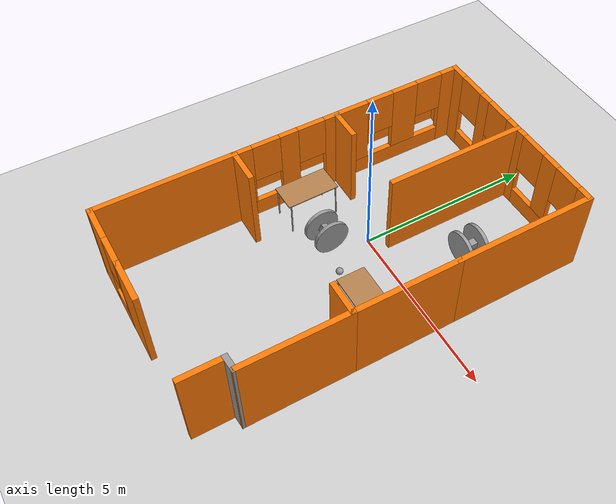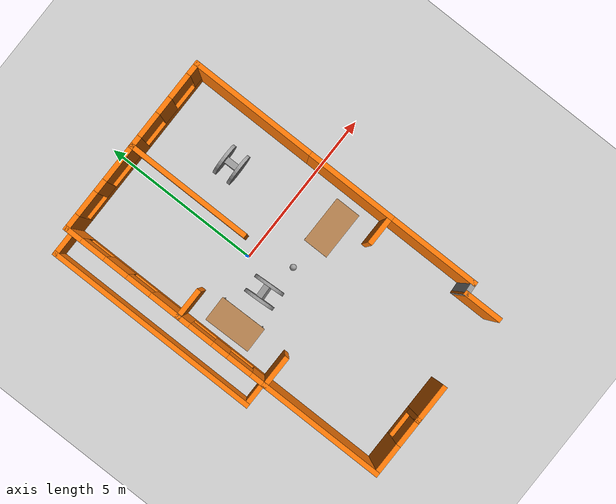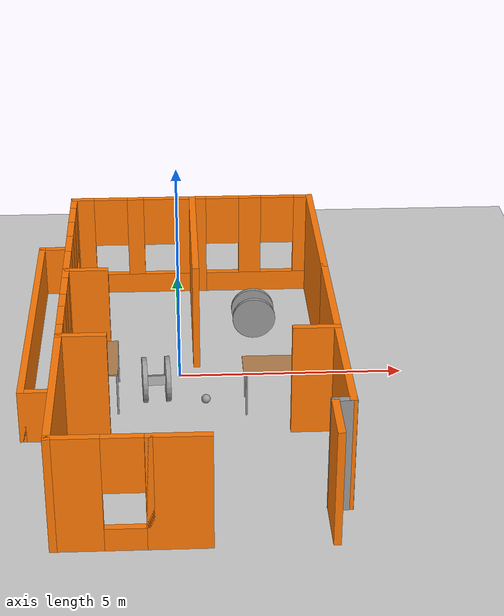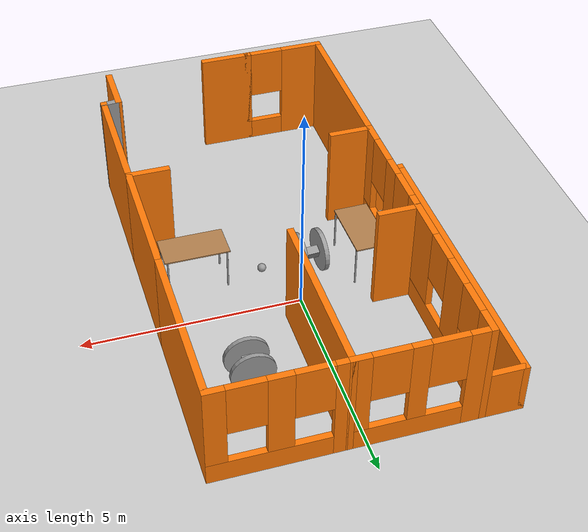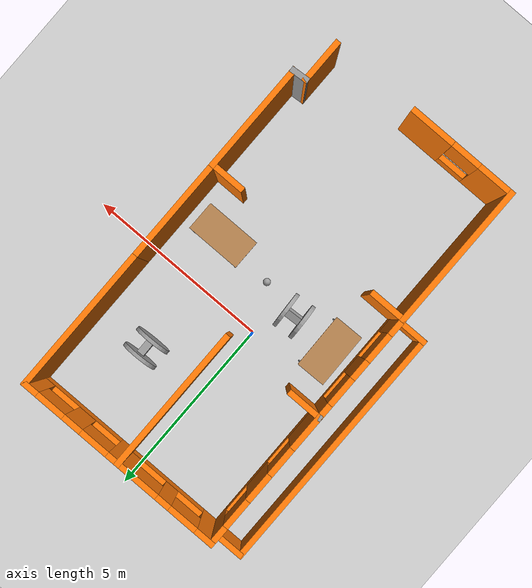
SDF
<sdf version="1.6">
 <world name="default">
  <plugin name="welcome" filename="libwelcome.so"/>
  <light name="sun" type="directional">
   <pose>0 0 10 0 -0 0</pose>
   <diffuse>0.8 0.8 0.8 1</diffuse>
   <specular>0.2 0.2 0.2 1</specular>
   <attenuation>
    <range>1000</range>
    <constant>0.9</constant>
    <linear>0.01</linear>
    <quadratic>0.001</quadratic>
   </attenuation>
   <direction>-0.5 0.1 -0.9</direction>
  </light>
  <model name="ground_plane">
   <static>1</static>
   <link name="link">
    <collision name="collision">
     <geometry><plane><normal>0 0 1</normal><size>100 100</size></plane></geometry>
     <surface>
      <contact><collide_bitmask>65535</collide_bitmask></contact>
      <friction><ode><mu>100</mu><mu2>50</mu2></ode></friction>
     </surface>
    </collision>
    <visual name="visual">
     <cast_shadows>0</cast_shadows>
     <geometry><plane><normal>0 0 1</normal><size>100 100</size></plane></geometry>
     <material>
      <script><uri>file://media/materials/scripts/gazebo.material</uri><name>Gazebo/Grey</name></script>
     </material>
    </visual>
   </link>
  </model>
  <gravity>0 0 -9.8</gravity>
  <magnetic_field>6e-06 2.3e-05 -4.2e-05</magnetic_field>
  <atmosphere type="adiabatic"/>
  <physics name="default_physics" default="0" type="ode">
   <max_step_size>0.001</max_step_size>
   <real_time_factor>1</real_time_factor>
   <real_time_update_rate>1000</real_time_update_rate>
  </physics>
  <scene><ambient>0.4 0.4 0.4 1</ambient><background>0.7 0.7 0.7 1</background><shadows>1</shadows></scene>
  <spherical_coordinates>
   <surface_model>EARTH_WGS84</surface_model>
   <latitude_deg>0</latitude_deg>
   <longitude_deg>0</longitude_deg>
   <elevation>0</elevation>
   <heading_deg>0</heading_deg>
  </spherical_coordinates>
  <model name="table">
   <static>1</static>
   <link name="link">
    <collision name="surface">
     <pose>0 0 1 0 -0 0</pose>
     <geometry><box><size>1.5 0.8 0.03</size></box></geometry>
     <surface><friction><ode><mu>0.6</mu><mu2>0.6</mu2></ode></friction></surface>
    </collision>
    <visual name="visual1">
     <pose>0 0 1 0 -0 0</pose>
     <geometry><box><size>1.5 0.8 0.03</size></box></geometry>
     <material>
      <script><uri>file://media/materials/scripts/gazebo.material</uri><name>Gazebo/Wood</name></script>
     </material>
    </visual>
    <collision name="front_left_leg">
     <pose>0.68 0.38 0.5 0 -0 0</pose>
     <geometry><cylinder><radius>0.02</radius><length>1</length></cylinder></geometry>
    </collision>
    <visual name="front_left_leg">
     <pose>0.68 0.38 0.5 0 -0 0</pose>
     <geometry><cylinder><radius>0.02</radius><length>1</length></cylinder></geometry>
     <material>
      <script><uri>file://media/materials/scripts/gazebo.material</uri><name>Gazebo/Grey</name></script>
     </material>
    </visual>
    <collision name="front_right_leg">
     <pose>0.68 -0.38 0.5 0 -0 0</pose>
     <geometry><cylinder><radius>0.02</radius><length>1</length></cylinder></geometry>
    </collision>
    <visual name="front_right_leg">
     <pose>0.68 -0.38 0.5 0 -0 0</pose>
     <geometry><cylinder><radius>0.02</radius><length>1</length></cylinder></geometry>
     <material>
      <script><uri>file://media/materials/scripts/gazebo.material</uri><name>Gazebo/Grey</name></script>
     </material>
    </visual>
    <collision name="back_right_leg">
     <pose>-0.68 -0.38 0.5 0 -0 0</pose>
     <geometry><cylinder><radius>0.02</radius><length>1</length></cylinder></geometry>
    </collision>
    <visual name="back_right_leg">
     <pose>-0.68 -0.38 0.5 0 -0 0</pose>
     <geometry><cylinder><radius>0.02</radius><length>1</length></cylinder></geometry>
     <material>
      <script><uri>file://media/materials/scripts/gazebo.material</uri><name>Gazebo/Grey</name></script>
     </material>
    </visual>
    <collision name="back_left_leg">
     <pose>-0.68 0.38 0.5 0 -0 0</pose>
     <geometry><cylinder><radius>0.02</radius><length>1</length></cylinder></geometry>
    </collision>
    <visual name="back_left_leg">
     <pose>-0.68 0.38 0.5 0 -0 0</pose>
     <geometry><cylinder><radius>0.02</radius><length>1</length></cylinder></geometry>
     <material>
      <script><uri>file://media/materials/scripts/gazebo.material</uri><name>Gazebo/Grey</name></script>
     </material>
    </visual>
   </link>
   <pose>-1.73141 -0.905015 0 0 0 -1.55569</pose>
  </model>
  <model name="table_clone">
   <static>1</static>
   <link name="link">
    <collision name="surface">
     <pose>0 0 1 0 -0 0</pose>
     <geometry><box><size>1.5 0.8 0.03</size></box></geometry>
     <surface><friction><ode><mu>0.6</mu><mu2>0.6</mu2></ode></friction></surface>
    </collision>
    <visual name="visual1">
     <pose>0 0 1 0 -0 0</pose>
     <geometry><box><size>1.5 0.8 0.03</size></box></geometry>
     <material>
      <script><uri>file://media/materials/scripts/gazebo.material</uri><name>Gazebo/Wood</name></script>
     </material>
    </visual>
    <collision name="front_left_leg">
     <pose>0.68 0.38 0.5 0 -0 0</pose>
     <geometry><cylinder><radius>0.02</radius><length>1</length></cylinder></geometry>
    </collision>
    <visual name="front_left_leg">
     <pose>0.68 0.38 0.5 0 -0 0</pose>
     <geometry><cylinder><radius>0.02</radius><length>1</length></cylinder></geometry>
     <material>
      <script><uri>file://media/materials/scripts/gazebo.material</uri><name>Gazebo/Grey</name></script>
     </material>
    </visual>
    <collision name="front_right_leg">
     <pose>0.68 -0.38 0.5 0 -0 0</pose>
     <geometry><cylinder><radius>0.02</radius><length>1</length></cylinder></geometry>
    </collision>
    <visual name="front_right_leg">
     <pose>0.68 -0.38 0.5 0 -0 0</pose>
     <geometry><cylinder><radius>0.02</radius><length>1</length></cylinder></geometry>
     <material>
      <script><uri>file://media/materials/scripts/gazebo.material</uri><name>Gazebo/Grey</name></script>
     </material>
    </visual>
    <collision name="back_right_leg">
     <pose>-0.68 -0.38 0.5 0 -0 0</pose>
     <geometry><cylinder><radius>0.02</radius><length>1</length></cylinder></geometry>
    </collision>
    <visual name="back_right_leg">
     <pose>-0.68 -0.38 0.5 0 -0 0</pose>
     <geometry><cylinder><radius>0.02</radius><length>1</length></cylinder></geometry>
     <material>
      <script><uri>file://media/materials/scripts/gazebo.material</uri><name>Gazebo/Grey</name></script>
     </material>
    </visual>
    <collision name="back_left_leg">
     <pose>-0.68 0.38 0.5 0 -0 0</pose>
     <geometry><cylinder><radius>0.02</radius><length>1</length></cylinder></geometry>
    </collision>
    <visual name="back_left_leg">
     <pose>-0.68 0.38 0.5 0 -0 0</pose>
     <geometry><cylinder><radius>0.02</radius><length>1</length></cylinder></geometry>
     <material>
      <script><uri>file://media/materials/scripts/gazebo.material</uri><name>Gazebo/Grey</name></script>
     </material>
    </visual>
   </link>
   <pose>2.1037 -1.35382 0 0 -0 0</pose>
  </model>
  <model name="myrobot">
   <link name="link_2">
    <pose>-0.013333 0 -0.013331 0 -0 0</pose>
    <inertial>
     <mass>1</mass>
     <inertia>
      <ixx>0.166667</ixx>
      <ixy>0</ixy>
      <ixz>0</ixz>
      <iyy>0.166667</iyy>
      <iyz>0</iyz>
      <izz>0.166667</izz>
     </inertia>
    </inertial>
    <visual name="visual">
     <geometry><box><size>0.2 0.4 0.2</size></box></geometry>
     <material>
      <lighting>1</lighting>
      <script><uri>file://media/materials/scripts/gazebo.material</uri><name>Gazebo/Grey</name></script>
      <shader type="pixel"><normal_map>__default__</normal_map></shader>
      <ambient>0.3 0.3 0.3 1</ambient>
      <diffuse>0.7 0.7 0.7 1</diffuse>
      <specular>0.01 0.01 0.01 1</specular>
      <emissive>0 0 0 1</emissive>
     </material>
    </visual>
    <collision name="collision">
     <geometry><box><size>0.2 0.4 0.2</size></box></geometry>
     <surface>
      <friction>
       <ode><mu>1</mu><mu2>1</mu2><fdir1>0 0 0</fdir1><slip1>0</slip1><slip2>0</slip2></ode>
       <torsional>
        <coefficient>1</coefficient>
        <patch_radius>0</patch_radius>
        <surface_radius>0</surface_radius>
        <use_patch_radius>1</use_patch_radius>
        <ode><slip>0</slip></ode>
       </torsional>
      </friction>
      <bounce><restitution_coefficient>0</restitution_coefficient><threshold>1e+06</threshold></bounce>
      <contact>
       <collide_without_contact>0</collide_without_contact>
       <collide_without_contact_bitmask>1</collide_without_contact_bitmask>
       <collide_bitmask>1</collide_bitmask>
       <ode>
        <soft_cfm>0</soft_cfm>
        <soft_erp>0.2</soft_erp>
        <kp>1e+13</kp>
        <kd>1</kd>
        <max_vel>0.01</max_vel>
        <min_depth>0</min_depth>
       </ode>
       <bullet>
        <split_impulse>1</split_impulse>
        <split_impulse_penetration_threshold>-0.01</split_impulse_penetration_threshold>
        <soft_cfm>0</soft_cfm>
        <soft_erp>0.2</soft_erp>
        <kp>1e+13</kp>
        <kd>1</kd>
       </bullet>
      </contact>
     </surface>
    </collision>
   </link>
   <link name="link_3">
    <pose>0.006667 -0.250048 0.006665 1.5707 -0 0</pose>
    <inertial>
     <mass>1</mass>
     <inertia><ixx>0.145833</ixx><ixy>0</ixy><ixz>0</ixz><iyy>0.145833</iyy><iyz>0</iyz><izz>0.125</izz></inertia>
    </inertial>
    <visual name="visual">
     <geometry><cylinder><radius>0.5</radius><length>0.1</length></cylinder></geometry>
     <material>
      <lighting>1</lighting>
      <script><uri>file://media/materials/scripts/gazebo.material</uri><name>Gazebo/Grey</name></script>
      <shader type="pixel"><normal_map>__default__</normal_map></shader>
      <ambient>0.3 0.3 0.3 1</ambient>
      <diffuse>0.7 0.7 0.7 1</diffuse>
      <specular>0.01 0.01 0.01 1</specular>
      <emissive>0 0 0 1</emissive>
     </material>
    </visual>
    <collision name="collision">
     <geometry><cylinder><radius>0.5</radius><length>0.1</length></cylinder></geometry>
     <surface>
      <friction>
       <ode><mu>1</mu><mu2>1</mu2><fdir1>0 0 0</fdir1><slip1>0</slip1><slip2>0</slip2></ode>
       <torsional>
        <coefficient>1</coefficient>
        <patch_radius>0</patch_radius>
        <surface_radius>0</surface_radius>
        <use_patch_radius>1</use_patch_radius>
        <ode><slip>0</slip></ode>
       </torsional>
      </friction>
      <bounce><restitution_coefficient>0</restitution_coefficient><threshold>1e+06</threshold></bounce>
      <contact>
       <collide_without_contact>0</collide_without_contact>
       <collide_without_contact_bitmask>1</collide_without_contact_bitmask>
       <collide_bitmask>1</collide_bitmask>
       <ode>
        <soft_cfm>0</soft_cfm>
        <soft_erp>0.2</soft_erp>
        <kp>1e+13</kp>
        <kd>1</kd>
        <max_vel>0.01</max_vel>
        <min_depth>0</min_depth>
       </ode>
       <bullet>
        <split_impulse>1</split_impulse>
        <split_impulse_penetration_threshold>-0.01</split_impulse_penetration_threshold>
        <soft_cfm>0</soft_cfm>
        <soft_erp>0.2</soft_erp>
        <kp>1e+13</kp>
        <kd>1</kd>
       </bullet>
      </contact>
     </surface>
    </collision>
   </link>
   <link name="link_3_clone">
    <pose>0.006667 0.250048 0.006669 1.5707 -0 0</pose>
    <inertial>
     <mass>1</mass>
     <inertia><ixx>0.145833</ixx><ixy>0</ixy><ixz>0</ixz><iyy>0.145833</iyy><iyz>0</iyz><izz>0.125</izz></inertia>
    </inertial>
    <visual name="visual">
     <geometry><cylinder><radius>0.5</radius><length>0.1</length></cylinder></geometry>
     <material>
      <lighting>1</lighting>
      <script><uri>file://media/materials/scripts/gazebo.material</uri><name>Gazebo/Grey</name></script>
      <shader type="pixel"><normal_map>__default__</normal_map></shader>
      <ambient>0.3 0.3 0.3 1</ambient>
      <diffuse>0.7 0.7 0.7 1</diffuse>
      <specular>0.01 0.01 0.01 1</specular>
      <emissive>0 0 0 1</emissive>
     </material>
    </visual>
    <collision name="collision">
     <geometry><cylinder><radius>0.5</radius><length>0.1</length></cylinder></geometry>
     <surface>
      <friction>
       <ode><mu>1</mu><mu2>1</mu2><fdir1>0 0 0</fdir1><slip1>0</slip1><slip2>0</slip2></ode>
       <torsional>
        <coefficient>1</coefficient>
        <patch_radius>0</patch_radius>
        <surface_radius>0</surface_radius>
        <use_patch_radius>1</use_patch_radius>
        <ode><slip>0</slip></ode>
       </torsional>
      </friction>
      <bounce><restitution_coefficient>0</restitution_coefficient><threshold>1e+06</threshold></bounce>
      <contact>
       <collide_without_contact>0</collide_without_contact>
       <collide_without_contact_bitmask>1</collide_without_contact_bitmask>
       <collide_bitmask>1</collide_bitmask>
       <ode>
        <soft_cfm>0</soft_cfm>
        <soft_erp>0.2</soft_erp>
        <kp>1e+13</kp>
        <kd>1</kd>
        <max_vel>0.01</max_vel>
        <min_depth>0</min_depth>
       </ode>
       <bullet>
        <split_impulse>1</split_impulse>
        <split_impulse_penetration_threshold>-0.01</split_impulse_penetration_threshold>
        <soft_cfm>0</soft_cfm>
        <soft_erp>0.2</soft_erp>
        <kp>1e+13</kp>
        <kd>1</kd>
       </bullet>
      </contact>
     </surface>
    </collision>
   </link>
   <joint name="link_2_JOINT_6" type="revolute">
    <parent>link_2</parent>
    <child>link_3</child>
    <axis>
     <xyz>0 0 -1</xyz>
     <use_parent_model_frame>0</use_parent_model_frame>
     <limit>
      <lower>-1.79769e+308</lower>
      <upper>1.79769e+308</upper>
      <effort>-1</effort>
      <velocity>-1</velocity>
     </limit>
     <dynamics>
      <spring_reference>0</spring_reference>
      <spring_stiffness>0</spring_stiffness>
      <damping>0</damping>
     </dynamics>
    </axis>
    <physics>
     <ode><limit><cfm>0</cfm><erp>0.2</erp></limit><suspension><cfm>0</cfm><erp>0.2</erp></suspension></ode>
    </physics>
   </joint>
   <joint name="link_2_JOINT_7" type="revolute">
    <parent>link_2</parent>
    <child>link_3_clone</child>
    <axis>
     <xyz>0 0 1</xyz>
     <use_parent_model_frame>0</use_parent_model_frame>
     <limit>
      <lower>-1.79769e+308</lower>
      <upper>1.79769e+308</upper>
      <effort>-1</effort>
      <velocity>-1</velocity>
     </limit>
     <dynamics>
      <spring_reference>0</spring_reference>
      <spring_stiffness>0</spring_stiffness>
      <damping>0</damping>
     </dynamics>
    </axis>
    <physics>
     <ode><limit><cfm>0</cfm><erp>0.2</erp></limit><suspension><cfm>0</cfm><erp>0.2</erp></suspension></ode>
    </physics>
   </joint>
   <static>0</static>
   <pose>-0.515429 -0.985947 0.491386 -8e-06 -0.367931 -1.51664</pose>
  </model>
  <model name="myrobot_0">
   <link name="link_2">
    <pose>-0.013333 0 -0.013331 0 -0 0</pose>
    <inertial>
     <mass>1</mass>
     <inertia>
      <ixx>0.166667</ixx>
      <ixy>0</ixy>
      <ixz>0</ixz>
      <iyy>0.166667</iyy>
      <iyz>0</iyz>
      <izz>0.166667</izz>
     </inertia>
    </inertial>
    <visual name="visual">
     <geometry><box><size>0.2 0.4 0.2</size></box></geometry>
     <material>
      <lighting>1</lighting>
      <script><uri>file://media/materials/scripts/gazebo.material</uri><name>Gazebo/Grey</name></script>
      <shader type="pixel"><normal_map>__default__</normal_map></shader>
      <ambient>0.3 0.3 0.3 1</ambient>
      <diffuse>0.7 0.7 0.7 1</diffuse>
      <specular>0.01 0.01 0.01 1</specular>
      <emissive>0 0 0 1</emissive>
     </material>
    </visual>
    <collision name="collision">
     <geometry><box><size>0.2 0.4 0.2</size></box></geometry>
     <surface>
      <friction>
       <ode><mu>1</mu><mu2>1</mu2><fdir1>0 0 0</fdir1><slip1>0</slip1><slip2>0</slip2></ode>
       <torsional>
        <coefficient>1</coefficient>
        <patch_radius>0</patch_radius>
        <surface_radius>0</surface_radius>
        <use_patch_radius>1</use_patch_radius>
        <ode><slip>0</slip></ode>
       </torsional>
      </friction>
      <bounce><restitution_coefficient>0</restitution_coefficient><threshold>1e+06</threshold></bounce>
      <contact>
       <collide_without_contact>0</collide_without_contact>
       <collide_without_contact_bitmask>1</collide_without_contact_bitmask>
       <collide_bitmask>1</collide_bitmask>
       <ode>
        <soft_cfm>0</soft_cfm>
        <soft_erp>0.2</soft_erp>
        <kp>1e+13</kp>
        <kd>1</kd>
        <max_vel>0.01</max_vel>
        <min_depth>0</min_depth>
       </ode>
       <bullet>
        <split_impulse>1</split_impulse>
        <split_impulse_penetration_threshold>-0.01</split_impulse_penetration_threshold>
        <soft_cfm>0</soft_cfm>
        <soft_erp>0.2</soft_erp>
        <kp>1e+13</kp>
        <kd>1</kd>
       </bullet>
      </contact>
     </surface>
    </collision>
   </link>
   <link name="link_3">
    <pose>0.006667 -0.250048 0.006665 1.5707 -0 0</pose>
    <inertial>
     <mass>1</mass>
     <inertia><ixx>0.145833</ixx><ixy>0</ixy><ixz>0</ixz><iyy>0.145833</iyy><iyz>0</iyz><izz>0.125</izz></inertia>
    </inertial>
    <visual name="visual">
     <geometry><cylinder><radius>0.5</radius><length>0.1</length></cylinder></geometry>
     <material>
      <lighting>1</lighting>
      <script><uri>file://media/materials/scripts/gazebo.material</uri><name>Gazebo/Grey</name></script>
      <shader type="pixel"><normal_map>__default__</normal_map></shader>
      <ambient>0.3 0.3 0.3 1</ambient>
      <diffuse>0.7 0.7 0.7 1</diffuse>
      <specular>0.01 0.01 0.01 1</specular>
      <emissive>0 0 0 1</emissive>
     </material>
    </visual>
    <collision name="collision">
     <geometry><cylinder><radius>0.5</radius><length>0.1</length></cylinder></geometry>
     <surface>
      <friction>
       <ode><mu>1</mu><mu2>1</mu2><fdir1>0 0 0</fdir1><slip1>0</slip1><slip2>0</slip2></ode>
       <torsional>
        <coefficient>1</coefficient>
        <patch_radius>0</patch_radius>
        <surface_radius>0</surface_radius>
        <use_patch_radius>1</use_patch_radius>
        <ode><slip>0</slip></ode>
       </torsional>
      </friction>
      <bounce><restitution_coefficient>0</restitution_coefficient><threshold>1e+06</threshold></bounce>
      <contact>
       <collide_without_contact>0</collide_without_contact>
       <collide_without_contact_bitmask>1</collide_without_contact_bitmask>
       <collide_bitmask>1</collide_bitmask>
       <ode>
        <soft_cfm>0</soft_cfm>
        <soft_erp>0.2</soft_erp>
        <kp>1e+13</kp>
        <kd>1</kd>
        <max_vel>0.01</max_vel>
        <min_depth>0</min_depth>
       </ode>
       <bullet>
        <split_impulse>1</split_impulse>
        <split_impulse_penetration_threshold>-0.01</split_impulse_penetration_threshold>
        <soft_cfm>0</soft_cfm>
        <soft_erp>0.2</soft_erp>
        <kp>1e+13</kp>
        <kd>1</kd>
       </bullet>
      </contact>
     </surface>
    </collision>
   </link>
   <link name="link_3_clone">
    <pose>0.006667 0.250048 0.006669 1.5707 -0 0</pose>
    <inertial>
     <mass>1</mass>
     <inertia><ixx>0.145833</ixx><ixy>0</ixy><ixz>0</ixz><iyy>0.145833</iyy><iyz>0</iyz><izz>0.125</izz></inertia>
    </inertial>
    <visual name="visual">
     <geometry><cylinder><radius>0.5</radius><length>0.1</length></cylinder></geometry>
     <material>
      <lighting>1</lighting>
      <script><uri>file://media/materials/scripts/gazebo.material</uri><name>Gazebo/Grey</name></script>
      <shader type="pixel"><normal_map>__default__</normal_map></shader>
      <ambient>0.3 0.3 0.3 1</ambient>
      <diffuse>0.7 0.7 0.7 1</diffuse>
      <specular>0.01 0.01 0.01 1</specular>
      <emissive>0 0 0 1</emissive>
     </material>
    </visual>
    <collision name="collision">
     <geometry><cylinder><radius>0.5</radius><length>0.1</length></cylinder></geometry>
     <surface>
      <friction>
       <ode><mu>1</mu><mu2>1</mu2><fdir1>0 0 0</fdir1><slip1>0</slip1><slip2>0</slip2></ode>
       <torsional>
        <coefficient>1</coefficient>
        <patch_radius>0</patch_radius>
        <surface_radius>0</surface_radius>
        <use_patch_radius>1</use_patch_radius>
        <ode><slip>0</slip></ode>
       </torsional>
      </friction>
      <bounce><restitution_coefficient>0</restitution_coefficient><threshold>1e+06</threshold></bounce>
      <contact>
       <collide_without_contact>0</collide_without_contact>
       <collide_without_contact_bitmask>1</collide_without_contact_bitmask>
       <collide_bitmask>1</collide_bitmask>
       <ode>
        <soft_cfm>0</soft_cfm>
        <soft_erp>0.2</soft_erp>
        <kp>1e+13</kp>
        <kd>1</kd>
        <max_vel>0.01</max_vel>
        <min_depth>0</min_depth>
       </ode>
       <bullet>
        <split_impulse>1</split_impulse>
        <split_impulse_penetration_threshold>-0.01</split_impulse_penetration_threshold>
        <soft_cfm>0</soft_cfm>
        <soft_erp>0.2</soft_erp>
        <kp>1e+13</kp>
        <kd>1</kd>
       </bullet>
      </contact>
     </surface>
    </collision>
   </link>
   <joint name="link_2_JOINT_6" type="revolute">
    <parent>link_2</parent>
    <child>link_3</child>
    <axis>
     <xyz>0 0 -1</xyz>
     <use_parent_model_frame>0</use_parent_model_frame>
     <limit>
      <lower>-1.79769e+308</lower>
      <upper>1.79769e+308</upper>
      <effort>-1</effort>
      <velocity>-1</velocity>
     </limit>
     <dynamics>
      <spring_reference>0</spring_reference>
      <spring_stiffness>0</spring_stiffness>
      <damping>0</damping>
     </dynamics>
    </axis>
    <physics>
     <ode><limit><cfm>0</cfm><erp>0.2</erp></limit><suspension><cfm>0</cfm><erp>0.2</erp></suspension></ode>
    </physics>
   </joint>
   <joint name="link_2_JOINT_7" type="revolute">
    <parent>link_2</parent>
    <child>link_3_clone</child>
    <axis>
     <xyz>0 0 1</xyz>
     <use_parent_model_frame>0</use_parent_model_frame>
     <limit>
      <lower>-1.79769e+308</lower>
      <upper>1.79769e+308</upper>
      <effort>-1</effort>
      <velocity>-1</velocity>
     </limit>
     <dynamics>
      <spring_reference>0</spring_reference>
      <spring_stiffness>0</spring_stiffness>
      <damping>0</damping>
     </dynamics>
    </axis>
    <physics>
     <ode><limit><cfm>0</cfm><erp>0.2</erp></limit><suspension><cfm>0</cfm><erp>0.2</erp></suspension></ode>
    </physics>
   </joint>
   <static>0</static>
   <pose>1.77326 2.01673 0.493029 -1e-06 -1.52398 0.018767</pose>
  </model>
  <model name="myhouse">
   <link name="Wall_1">
    <pose>-3.27785 1.94213 0 0 0 -1.5708</pose>
    <visual name="Wall_1_Visual">
     <pose>0 0 0.6 0 -0 0</pose>
     <geometry><box><size>7 0.15 1.2</size></box></geometry>
     <material>
      <script><uri>file://media/materials/scripts/gazebo.material</uri><name>Gazebo/Grey</name></script>
      <ambient>0.996078 0.47451 0.0196078 1</ambient>
      <shader type="pixel"/>
      <diffuse>0.7 0.7 0.7 1</diffuse>
      <specular>0.01 0.01 0.01 1</specular>
      <emissive>0 0 0 1</emissive>
     </material>
     <meta><layer>0</layer></meta>
    </visual>
    <collision name="Wall_1_Collision">
     <pose>0 0 0.6 0 -0 0</pose>
     <geometry><box><size>7 0.15 1.2</size></box></geometry>
     <surface>
      <friction>
       <ode><mu>1</mu><mu2>1</mu2><fdir1>0 0 0</fdir1><slip1>0</slip1><slip2>0</slip2></ode>
       <torsional>
        <coefficient>1</coefficient>
        <patch_radius>0</patch_radius>
        <surface_radius>0</surface_radius>
        <use_patch_radius>1</use_patch_radius>
        <ode><slip>0</slip></ode>
       </torsional>
      </friction>
      <bounce><restitution_coefficient>0</restitution_coefficient><threshold>1e+06</threshold></bounce>
      <contact>
       <collide_without_contact>0</collide_without_contact>
       <collide_without_contact_bitmask>1</collide_without_contact_bitmask>
       <collide_bitmask>1</collide_bitmask>
       <ode>
        <soft_cfm>0</soft_cfm>
        <soft_erp>0.2</soft_erp>
        <kp>1e+13</kp>
        <kd>1</kd>
        <max_vel>0.01</max_vel>
        <min_depth>0</min_depth>
       </ode>
       <bullet>
        <split_impulse>1</split_impulse>
        <split_impulse_penetration_threshold>-0.01</split_impulse_penetration_threshold>
        <soft_cfm>0</soft_cfm>
        <soft_erp>0.2</soft_erp>
        <kp>1e+13</kp>
        <kd>1</kd>
       </bullet>
      </contact>
     </surface>
    </collision>
   </link>
   <link name="Wall_10">
    <pose>1.84738 5.36737 0 0 -0 0</pose>
    <visual name="Wall_10_Visual_0">
     <pose>-1.2952 0 1.25 0 -0 0</pose>
     <geometry><box><size>0.409593 0.15 2.5</size></box></geometry>
     <material>
      <script><uri>file://media/materials/scripts/gazebo.material</uri><name>Gazebo/Grey</name></script>
      <ambient>0.996078 0.47451 0.0196078 1</ambient>
      <shader type="pixel"/>
      <diffuse>0.7 0.7 0.7 1</diffuse>
      <specular>0.01 0.01 0.01 1</specular>
      <emissive>0 0 0 1</emissive>
     </material>
     <meta><layer>0</layer></meta>
    </visual>
    <visual name="Wall_10_Visual_1">
     <pose>0.204797 0 0.25 0 -0 0</pose>
     <geometry><box><size>2.59041 0.15 0.5</size></box></geometry>
     <material>
      <script><uri>file://media/materials/scripts/gazebo.material</uri><name>Gazebo/Grey</name></script>
      <ambient>0.996078 0.47451 0.0196078 1</ambient>
      <shader type="pixel"/>
      <diffuse>0.7 0.7 0.7 1</diffuse>
      <specular>0.01 0.01 0.01 1</specular>
      <emissive>0 0 0 1</emissive>
     </material>
     <meta><layer>0</layer></meta>
    </visual>
    <visual name="Wall_10_Visual_2">
     <pose>-0.02201 0 1.5 0 -0 0</pose>
     <geometry><box><size>0.536793 0.15 2</size></box></geometry>
     <material>
      <script><uri>file://media/materials/scripts/gazebo.material</uri><name>Gazebo/Grey</name></script>
      <ambient>0.996078 0.47451 0.0196078 1</ambient>
      <shader type="pixel"/>
      <diffuse>0.7 0.7 0.7 1</diffuse>
      <specular>0.01 0.01 0.01 1</specular>
      <emissive>0 0 0 1</emissive>
     </material>
     <meta><layer>0</layer></meta>
    </visual>
    <visual name="Wall_10_Visual_3">
     <pose>1.27319 0 1.5 0 -0 0</pose>
     <geometry><box><size>0.453614 0.15 2</size></box></geometry>
     <material>
      <script><uri>file://media/materials/scripts/gazebo.material</uri><name>Gazebo/Grey</name></script>
      <ambient>0.996078 0.47451 0.0196078 1</ambient>
      <shader type="pixel"/>
      <diffuse>0.7 0.7 0.7 1</diffuse>
      <specular>0.01 0.01 0.01 1</specular>
      <emissive>0 0 0 1</emissive>
     </material>
     <meta><layer>0</layer></meta>
    </visual>
    <visual name="Wall_10_Visual_4">
     <pose>-0.690407 0 1.9 0 -0 0</pose>
     <geometry><box><size>0.8 0.15 1.2</size></box></geometry>
     <material>
      <script><uri>file://media/materials/scripts/gazebo.material</uri><name>Gazebo/Grey</name></script>
      <ambient>0.996078 0.47451 0.0196078 1</ambient>
      <shader type="pixel"/>
      <diffuse>0.7 0.7 0.7 1</diffuse>
      <specular>0.01 0.01 0.01 1</specular>
      <emissive>0 0 0 1</emissive>
     </material>
     <meta><layer>0</layer></meta>
    </visual>
    <visual name="Wall_10_Visual_5">
     <pose>0.646386 0 1.9 0 -0 0</pose>
     <geometry><box><size>0.8 0.15 1.2</size></box></geometry>
     <material>
      <script><uri>file://media/materials/scripts/gazebo.material</uri><name>Gazebo/Grey</name></script>
      <ambient>0.996078 0.47451 0.0196078 1</ambient>
      <shader type="pixel"/>
      <diffuse>0.7 0.7 0.7 1</diffuse>
      <specular>0.01 0.01 0.01 1</specular>
      <emissive>0 0 0 1</emissive>
     </material>
     <meta><layer>0</layer></meta>
    </visual>
    <collision name="Wall_10_Collision_0">
     <pose>-1.2952 0 1.25 0 -0 0</pose>
     <geometry><box><size>0.409593 0.15 2.5</size></box></geometry>
     <surface>
      <friction>
       <ode><mu>1</mu><mu2>1</mu2><fdir1>0 0 0</fdir1><slip1>0</slip1><slip2>0</slip2></ode>
       <torsional>
        <coefficient>1</coefficient>
        <patch_radius>0</patch_radius>
        <surface_radius>0</surface_radius>
        <use_patch_radius>1</use_patch_radius>
        <ode><slip>0</slip></ode>
       </torsional>
      </friction>
      <bounce><restitution_coefficient>0</restitution_coefficient><threshold>1e+06</threshold></bounce>
      <contact>
       <collide_without_contact>0</collide_without_contact>
       <collide_without_contact_bitmask>1</collide_without_contact_bitmask>
       <collide_bitmask>1</collide_bitmask>
       <ode>
        <soft_cfm>0</soft_cfm>
        <soft_erp>0.2</soft_erp>
        <kp>1e+13</kp>
        <kd>1</kd>
        <max_vel>0.01</max_vel>
        <min_depth>0</min_depth>
       </ode>
       <bullet>
        <split_impulse>1</split_impulse>
        <split_impulse_penetration_threshold>-0.01</split_impulse_penetration_threshold>
        <soft_cfm>0</soft_cfm>
        <soft_erp>0.2</soft_erp>
        <kp>1e+13</kp>
        <kd>1</kd>
       </bullet>
      </contact>
     </surface>
    </collision>
    <collision name="Wall_10_Collision_2">
     <pose>-0.02201 0 1.5 0 -0 0</pose>
     <geometry><box><size>0.536793 0.15 2</size></box></geometry>
     <surface>
      <friction>
       <ode><mu>1</mu><mu2>1</mu2><fdir1>0 0 0</fdir1><slip1>0</slip1><slip2>0</slip2></ode>
       <torsional>
        <coefficient>1</coefficient>
        <patch_radius>0</patch_radius>
        <surface_radius>0</surface_radius>
        <use_patch_radius>1</use_patch_radius>
        <ode><slip>0</slip></ode>
       </torsional>
      </friction>
      <bounce><restitution_coefficient>0</restitution_coefficient><threshold>1e+06</threshold></bounce>
      <contact>
       <collide_without_contact>0</collide_without_contact>
       <collide_without_contact_bitmask>1</collide_without_contact_bitmask>
       <collide_bitmask>1</collide_bitmask>
       <ode>
        <soft_cfm>0</soft_cfm>
        <soft_erp>0.2</soft_erp>
        <kp>1e+13</kp>
        <kd>1</kd>
        <max_vel>0.01</max_vel>
        <min_depth>0</min_depth>
       </ode>
       <bullet>
        <split_impulse>1</split_impulse>
        <split_impulse_penetration_threshold>-0.01</split_impulse_penetration_threshold>
        <soft_cfm>0</soft_cfm>
        <soft_erp>0.2</soft_erp>
        <kp>1e+13</kp>
        <kd>1</kd>
       </bullet>
      </contact>
     </surface>
    </collision>
    <collision name="Wall_10_Collision_1">
     <pose>0.204797 0 0.25 0 -0 0</pose>
     <geometry><box><size>2.59041 0.15 0.5</size></box></geometry>
     <surface>
      <friction>
       <ode><mu>1</mu><mu2>1</mu2><fdir1>0 0 0</fdir1><slip1>0</slip1><slip2>0</slip2></ode>
       <torsional>
        <coefficient>1</coefficient>
        <patch_radius>0</patch_radius>
        <surface_radius>0</surface_radius>
        <use_patch_radius>1</use_patch_radius>
        <ode><slip>0</slip></ode>
       </torsional>
      </friction>
      <bounce><restitution_coefficient>0</restitution_coefficient><threshold>1e+06</threshold></bounce>
      <contact>
       <collide_without_contact>0</collide_without_contact>
       <collide_without_contact_bitmask>1</collide_without_contact_bitmask>
       <collide_bitmask>1</collide_bitmask>
       <ode>
        <soft_cfm>0</soft_cfm>
        <soft_erp>0.2</soft_erp>
        <kp>1e+13</kp>
        <kd>1</kd>
        <max_vel>0.01</max_vel>
        <min_depth>0</min_depth>
       </ode>
       <bullet>
        <split_impulse>1</split_impulse>
        <split_impulse_penetration_threshold>-0.01</split_impulse_penetration_threshold>
        <soft_cfm>0</soft_cfm>
        <soft_erp>0.2</soft_erp>
        <kp>1e+13</kp>
        <kd>1</kd>
       </bullet>
      </contact>
     </surface>
    </collision>
    <collision name="Wall_10_Collision_3">
     <pose>1.27319 0 1.5 0 -0 0</pose>
     <geometry><box><size>0.453614 0.15 2</size></box></geometry>
     <surface>
      <friction>
       <ode><mu>1</mu><mu2>1</mu2><fdir1>0 0 0</fdir1><slip1>0</slip1><slip2>0</slip2></ode>
       <torsional>
        <coefficient>1</coefficient>
        <patch_radius>0</patch_radius>
        <surface_radius>0</surface_radius>
        <use_patch_radius>1</use_patch_radius>
        <ode><slip>0</slip></ode>
       </torsional>
      </friction>
      <bounce><restitution_coefficient>0</restitution_coefficient><threshold>1e+06</threshold></bounce>
      <contact>
       <collide_without_contact>0</collide_without_contact>
       <collide_without_contact_bitmask>1</collide_without_contact_bitmask>
       <collide_bitmask>1</collide_bitmask>
       <ode>
        <soft_cfm>0</soft_cfm>
        <soft_erp>0.2</soft_erp>
        <kp>1e+13</kp>
        <kd>1</kd>
        <max_vel>0.01</max_vel>
        <min_depth>0</min_depth>
       </ode>
       <bullet>
        <split_impulse>1</split_impulse>
        <split_impulse_penetration_threshold>-0.01</split_impulse_penetration_threshold>
        <soft_cfm>0</soft_cfm>
        <soft_erp>0.2</soft_erp>
        <kp>1e+13</kp>
        <kd>1</kd>
       </bullet>
      </contact>
     </surface>
    </collision>
    <collision name="Wall_10_Collision_4">
     <pose>-0.690407 0 1.9 0 -0 0</pose>
     <geometry><box><size>0.8 0.15 1.2</size></box></geometry>
     <surface>
      <friction>
       <ode><mu>1</mu><mu2>1</mu2><fdir1>0 0 0</fdir1><slip1>0</slip1><slip2>0</slip2></ode>
       <torsional>
        <coefficient>1</coefficient>
        <patch_radius>0</patch_radius>
        <surface_radius>0</surface_radius>
        <use_patch_radius>1</use_patch_radius>
        <ode><slip>0</slip></ode>
       </torsional>
      </friction>
      <bounce><restitution_coefficient>0</restitution_coefficient><threshold>1e+06</threshold></bounce>
      <contact>
       <collide_without_contact>0</collide_without_contact>
       <collide_without_contact_bitmask>1</collide_without_contact_bitmask>
       <collide_bitmask>1</collide_bitmask>
       <ode>
        <soft_cfm>0</soft_cfm>
        <soft_erp>0.2</soft_erp>
        <kp>1e+13</kp>
        <kd>1</kd>
        <max_vel>0.01</max_vel>
        <min_depth>0</min_depth>
       </ode>
       <bullet>
        <split_impulse>1</split_impulse>
        <split_impulse_penetration_threshold>-0.01</split_impulse_penetration_threshold>
        <soft_cfm>0</soft_cfm>
        <soft_erp>0.2</soft_erp>
        <kp>1e+13</kp>
        <kd>1</kd>
       </bullet>
      </contact>
     </surface>
    </collision>
    <collision name="Wall_10_Collision_5">
     <pose>0.646386 0 1.9 0 -0 0</pose>
     <geometry><box><size>0.8 0.15 1.2</size></box></geometry>
     <surface>
      <friction>
       <ode><mu>1</mu><mu2>1</mu2><fdir1>0 0 0</fdir1><slip1>0</slip1><slip2>0</slip2></ode>
       <torsional>
        <coefficient>1</coefficient>
        <patch_radius>0</patch_radius>
        <surface_radius>0</surface_radius>
        <use_patch_radius>1</use_patch_radius>
        <ode><slip>0</slip></ode>
       </torsional>
      </friction>
      <bounce><restitution_coefficient>0</restitution_coefficient><threshold>1e+06</threshold></bounce>
      <contact>
       <collide_without_contact>0</collide_without_contact>
       <collide_without_contact_bitmask>1</collide_without_contact_bitmask>
       <collide_bitmask>1</collide_bitmask>
       <ode>
        <soft_cfm>0</soft_cfm>
        <soft_erp>0.2</soft_erp>
        <kp>1e+13</kp>
        <kd>1</kd>
        <max_vel>0.01</max_vel>
        <min_depth>0</min_depth>
       </ode>
       <bullet>
        <split_impulse>1</split_impulse>
        <split_impulse_penetration_threshold>-0.01</split_impulse_penetration_threshold>
        <soft_cfm>0</soft_cfm>
        <soft_erp>0.2</soft_erp>
        <kp>1e+13</kp>
        <kd>1</kd>
       </bullet>
      </contact>
     </surface>
    </collision>
   </link>
   <link name="Wall_11">
    <pose>3.27238 3.44237 0 0 0 -1.5708</pose>
    <visual name="Wall_11_Visual">
     <pose>0 0 1.25 0 -0 0</pose>
     <geometry><box><size>4 0.15 2.5</size></box></geometry>
     <material>
      <script><uri>file://media/materials/scripts/gazebo.material</uri><name>Gazebo/Grey</name></script>
      <ambient>0.996078 0.47451 0.0196078 1</ambient>
      <shader type="pixel"/>
      <diffuse>0.7 0.7 0.7 1</diffuse>
      <specular>0.01 0.01 0.01 1</specular>
      <emissive>0 0 0 1</emissive>
     </material>
     <meta><layer>0</layer></meta>
    </visual>
    <collision name="Wall_11_Collision">
     <pose>0 0 1.25 0 -0 0</pose>
     <geometry><box><size>4 0.15 2.5</size></box></geometry>
     <surface>
      <friction>
       <ode><mu>1</mu><mu2>1</mu2><fdir1>0 0 0</fdir1><slip1>0</slip1><slip2>0</slip2></ode>
       <torsional>
        <coefficient>1</coefficient>
        <patch_radius>0</patch_radius>
        <surface_radius>0</surface_radius>
        <use_patch_radius>1</use_patch_radius>
        <ode><slip>0</slip></ode>
       </torsional>
      </friction>
      <bounce><restitution_coefficient>0</restitution_coefficient><threshold>1e+06</threshold></bounce>
      <contact>
       <collide_without_contact>0</collide_without_contact>
       <collide_without_contact_bitmask>1</collide_without_contact_bitmask>
       <collide_bitmask>1</collide_bitmask>
       <ode>
        <soft_cfm>0</soft_cfm>
        <soft_erp>0.2</soft_erp>
        <kp>1e+13</kp>
        <kd>1</kd>
        <max_vel>0.01</max_vel>
        <min_depth>0</min_depth>
       </ode>
       <bullet>
        <split_impulse>1</split_impulse>
        <split_impulse_penetration_threshold>-0.01</split_impulse_penetration_threshold>
        <soft_cfm>0</soft_cfm>
        <soft_erp>0.2</soft_erp>
        <kp>1e+13</kp>
        <kd>1</kd>
       </bullet>
      </contact>
     </surface>
    </collision>
   </link>
   <link name="Wall_12">
    <pose>3.27238 0.092367 0 0 0 -1.5708</pose>
    <visual name="Wall_12_Visual">
     <pose>0 0 1.25 0 -0 0</pose>
     <geometry><box><size>3 0.15 2.5</size></box></geometry>
     <material>
      <script><uri>file://media/materials/scripts/gazebo.material</uri><name>Gazebo/Grey</name></script>
      <ambient>0.996078 0.47451 0.0196078 1</ambient>
      <shader type="pixel"/>
      <diffuse>0.7 0.7 0.7 1</diffuse>
      <specular>0.01 0.01 0.01 1</specular>
      <emissive>0 0 0 1</emissive>
     </material>
     <meta><layer>0</layer></meta>
    </visual>
    <collision name="Wall_12_Collision">
     <pose>0 0 1.25 0 -0 0</pose>
     <geometry><box><size>3 0.15 2.5</size></box></geometry>
     <surface>
      <friction>
       <ode><mu>1</mu><mu2>1</mu2><fdir1>0 0 0</fdir1><slip1>0</slip1><slip2>0</slip2></ode>
       <torsional>
        <coefficient>1</coefficient>
        <patch_radius>0</patch_radius>
        <surface_radius>0</surface_radius>
        <use_patch_radius>1</use_patch_radius>
        <ode><slip>0</slip></ode>
       </torsional>
      </friction>
      <bounce><restitution_coefficient>0</restitution_coefficient><threshold>1e+06</threshold></bounce>
      <contact>
       <collide_without_contact>0</collide_without_contact>
       <collide_without_contact_bitmask>1</collide_without_contact_bitmask>
       <collide_bitmask>1</collide_bitmask>
       <ode>
        <soft_cfm>0</soft_cfm>
        <soft_erp>0.2</soft_erp>
        <kp>1e+13</kp>
        <kd>1</kd>
        <max_vel>0.01</max_vel>
        <min_depth>0</min_depth>
       </ode>
       <bullet>
        <split_impulse>1</split_impulse>
        <split_impulse_penetration_threshold>-0.01</split_impulse_penetration_threshold>
        <soft_cfm>0</soft_cfm>
        <soft_erp>0.2</soft_erp>
        <kp>1e+13</kp>
        <kd>1</kd>
       </bullet>
      </contact>
     </surface>
    </collision>
   </link>
   <link name="Wall_15">
    <pose>0.422384 3.44237 0 0 0 -1.5708</pose>
    <visual name="Wall_15_Visual">
     <pose>0 0 1.25 0 -0 0</pose>
     <geometry><box><size>4 0.15 2.5</size></box></geometry>
     <material>
      <script><uri>file://media/materials/scripts/gazebo.material</uri><name>Gazebo/Grey</name></script>
      <ambient>0.996078 0.47451 0.0196078 1</ambient>
      <shader type="pixel"/>
      <diffuse>0.7 0.7 0.7 1</diffuse>
      <specular>0.01 0.01 0.01 1</specular>
      <emissive>0 0 0 1</emissive>
     </material>
     <meta><layer>0</layer></meta>
    </visual>
    <collision name="Wall_15_Collision">
     <pose>0 0 1.25 0 -0 0</pose>
     <geometry><box><size>4 0.15 2.5</size></box></geometry>
     <surface>
      <friction>
       <ode><mu>1</mu><mu2>1</mu2><fdir1>0 0 0</fdir1><slip1>0</slip1><slip2>0</slip2></ode>
       <torsional>
        <coefficient>1</coefficient>
        <patch_radius>0</patch_radius>
        <surface_radius>0</surface_radius>
        <use_patch_radius>1</use_patch_radius>
        <ode><slip>0</slip></ode>
       </torsional>
      </friction>
      <bounce><restitution_coefficient>0</restitution_coefficient><threshold>1e+06</threshold></bounce>
      <contact>
       <collide_without_contact>0</collide_without_contact>
       <collide_without_contact_bitmask>1</collide_without_contact_bitmask>
       <collide_bitmask>1</collide_bitmask>
       <ode>
        <soft_cfm>0</soft_cfm>
        <soft_erp>0.2</soft_erp>
        <kp>1e+13</kp>
        <kd>1</kd>
        <max_vel>0.01</max_vel>
        <min_depth>0</min_depth>
       </ode>
       <bullet>
        <split_impulse>1</split_impulse>
        <split_impulse_penetration_threshold>-0.01</split_impulse_penetration_threshold>
        <soft_cfm>0</soft_cfm>
        <soft_erp>0.2</soft_erp>
        <kp>1e+13</kp>
        <kd>1</kd>
       </bullet>
      </contact>
     </surface>
    </collision>
   </link>
   <link name="Wall_17">
    <pose>-2.42773 3.44225 0 0 0 -1.57073</pose>
    <visual name="Wall_17_Visual_0">
     <pose>-1.71028 0 1.25 0 -0 0</pose>
     <geometry><box><size>0.579442 0.15 2.5</size></box></geometry>
     <material>
      <script><uri>file://media/materials/scripts/gazebo.material</uri><name>Gazebo/Grey</name></script>
      <ambient>0.996078 0.47451 0.0196078 1</ambient>
      <shader type="pixel"/>
      <diffuse>0.7 0.7 0.7 1</diffuse>
      <specular>0.01 0.01 0.01 1</specular>
      <emissive>0 0 0 1</emissive>
     </material>
     <meta><layer>0</layer></meta>
    </visual>
    <visual name="Wall_17_Visual_1">
     <pose>0.289721 0 0.25 0 -0 0</pose>
     <geometry><box><size>3.42056 0.15 0.5</size></box></geometry>
     <material>
      <script><uri>file://media/materials/scripts/gazebo.material</uri><name>Gazebo/Grey</name></script>
      <ambient>0.996078 0.47451 0.0196078 1</ambient>
      <shader type="pixel"/>
      <diffuse>0.7 0.7 0.7 1</diffuse>
      <specular>0.01 0.01 0.01 1</specular>
      <emissive>0 0 0 1</emissive>
     </material>
     <meta><layer>0</layer></meta>
    </visual>
    <visual name="Wall_17_Visual_2">
     <pose>-0.229084 0 1.5 0 -0 0</pose>
     <geometry><box><size>0.782948 0.15 2</size></box></geometry>
     <material>
      <script><uri>file://media/materials/scripts/gazebo.material</uri><name>Gazebo/Grey</name></script>
      <ambient>0.996078 0.47451 0.0196078 1</ambient>
      <shader type="pixel"/>
      <diffuse>0.7 0.7 0.7 1</diffuse>
      <specular>0.01 0.01 0.01 1</specular>
      <emissive>0 0 0 1</emissive>
     </material>
     <meta><layer>0</layer></meta>
    </visual>
    <visual name="Wall_17_Visual_3">
     <pose>1.4812 0 1.5 0 -0 0</pose>
     <geometry><box><size>1.03761 0.15 2</size></box></geometry>
     <material>
      <script><uri>file://media/materials/scripts/gazebo.material</uri><name>Gazebo/Grey</name></script>
      <ambient>0.996078 0.47451 0.0196078 1</ambient>
      <shader type="pixel"/>
      <diffuse>0.7 0.7 0.7 1</diffuse>
      <specular>0.01 0.01 0.01 1</specular>
      <emissive>0 0 0 1</emissive>
     </material>
     <meta><layer>0</layer></meta>
    </visual>
    <visual name="Wall_17_Visual_4">
     <pose>-1.02056 0 1.9 0 -0 0</pose>
     <geometry><box><size>0.8 0.15 1.2</size></box></geometry>
     <material>
      <script><uri>file://media/materials/scripts/gazebo.material</uri><name>Gazebo/Grey</name></script>
      <ambient>0.996078 0.47451 0.0196078 1</ambient>
      <shader type="pixel"/>
      <diffuse>0.7 0.7 0.7 1</diffuse>
      <specular>0.01 0.01 0.01 1</specular>
      <emissive>0 0 0 1</emissive>
     </material>
     <meta><layer>0</layer></meta>
    </visual>
    <visual name="Wall_17_Visual_5">
     <pose>0.562389 0 1.9 0 -0 0</pose>
     <geometry><box><size>0.8 0.15 1.2</size></box></geometry>
     <material>
      <script><uri>file://media/materials/scripts/gazebo.material</uri><name>Gazebo/Grey</name></script>
      <ambient>0.996078 0.47451 0.0196078 1</ambient>
      <shader type="pixel"/>
      <diffuse>0.7 0.7 0.7 1</diffuse>
      <specular>0.01 0.01 0.01 1</specular>
      <emissive>0 0 0 1</emissive>
     </material>
     <meta><layer>0</layer></meta>
    </visual>
    <collision name="Wall_17_Collision_0">
     <pose>-1.71028 0 1.25 0 -0 0</pose>
     <geometry><box><size>0.579442 0.15 2.5</size></box></geometry>
     <surface>
      <friction>
       <ode><mu>1</mu><mu2>1</mu2><fdir1>0 0 0</fdir1><slip1>0</slip1><slip2>0</slip2></ode>
       <torsional>
        <coefficient>1</coefficient>
        <patch_radius>0</patch_radius>
        <surface_radius>0</surface_radius>
        <use_patch_radius>1</use_patch_radius>
        <ode><slip>0</slip></ode>
       </torsional>
      </friction>
      <bounce><restitution_coefficient>0</restitution_coefficient><threshold>1e+06</threshold></bounce>
      <contact>
       <collide_without_contact>0</collide_without_contact>
       <collide_without_contact_bitmask>1</collide_without_contact_bitmask>
       <collide_bitmask>1</collide_bitmask>
       <ode>
        <soft_cfm>0</soft_cfm>
        <soft_erp>0.2</soft_erp>
        <kp>1e+13</kp>
        <kd>1</kd>
        <max_vel>0.01</max_vel>
        <min_depth>0</min_depth>
       </ode>
       <bullet>
        <split_impulse>1</split_impulse>
        <split_impulse_penetration_threshold>-0.01</split_impulse_penetration_threshold>
        <soft_cfm>0</soft_cfm>
        <soft_erp>0.2</soft_erp>
        <kp>1e+13</kp>
        <kd>1</kd>
       </bullet>
      </contact>
     </surface>
    </collision>
    <collision name="Wall_17_Collision_5">
     <pose>0.562389 0 1.9 0 -0 0</pose>
     <geometry><box><size>0.8 0.15 1.2</size></box></geometry>
     <surface>
      <friction>
       <ode><mu>1</mu><mu2>1</mu2><fdir1>0 0 0</fdir1><slip1>0</slip1><slip2>0</slip2></ode>
       <torsional>
        <coefficient>1</coefficient>
        <patch_radius>0</patch_radius>
        <surface_radius>0</surface_radius>
        <use_patch_radius>1</use_patch_radius>
        <ode><slip>0</slip></ode>
       </torsional>
      </friction>
      <bounce><restitution_coefficient>0</restitution_coefficient><threshold>1e+06</threshold></bounce>
      <contact>
       <collide_without_contact>0</collide_without_contact>
       <collide_without_contact_bitmask>1</collide_without_contact_bitmask>
       <collide_bitmask>1</collide_bitmask>
       <ode>
        <soft_cfm>0</soft_cfm>
        <soft_erp>0.2</soft_erp>
        <kp>1e+13</kp>
        <kd>1</kd>
        <max_vel>0.01</max_vel>
        <min_depth>0</min_depth>
       </ode>
       <bullet>
        <split_impulse>1</split_impulse>
        <split_impulse_penetration_threshold>-0.01</split_impulse_penetration_threshold>
        <soft_cfm>0</soft_cfm>
        <soft_erp>0.2</soft_erp>
        <kp>1e+13</kp>
        <kd>1</kd>
       </bullet>
      </contact>
     </surface>
    </collision>
    <collision name="Wall_17_Collision_3">
     <pose>1.4812 0 1.5 0 -0 0</pose>
     <geometry><box><size>1.03761 0.15 2</size></box></geometry>
     <surface>
      <friction>
       <ode><mu>1</mu><mu2>1</mu2><fdir1>0 0 0</fdir1><slip1>0</slip1><slip2>0</slip2></ode>
       <torsional>
        <coefficient>1</coefficient>
        <patch_radius>0</patch_radius>
        <surface_radius>0</surface_radius>
        <use_patch_radius>1</use_patch_radius>
        <ode><slip>0</slip></ode>
       </torsional>
      </friction>
      <bounce><restitution_coefficient>0</restitution_coefficient><threshold>1e+06</threshold></bounce>
      <contact>
       <collide_without_contact>0</collide_without_contact>
       <collide_without_contact_bitmask>1</collide_without_contact_bitmask>
       <collide_bitmask>1</collide_bitmask>
       <ode>
        <soft_cfm>0</soft_cfm>
        <soft_erp>0.2</soft_erp>
        <kp>1e+13</kp>
        <kd>1</kd>
        <max_vel>0.01</max_vel>
        <min_depth>0</min_depth>
       </ode>
       <bullet>
        <split_impulse>1</split_impulse>
        <split_impulse_penetration_threshold>-0.01</split_impulse_penetration_threshold>
        <soft_cfm>0</soft_cfm>
        <soft_erp>0.2</soft_erp>
        <kp>1e+13</kp>
        <kd>1</kd>
       </bullet>
      </contact>
     </surface>
    </collision>
    <collision name="Wall_17_Collision_1">
     <pose>0.289721 0 0.25 0 -0 0</pose>
     <geometry><box><size>3.42056 0.15 0.5</size></box></geometry>
     <surface>
      <friction>
       <ode><mu>1</mu><mu2>1</mu2><fdir1>0 0 0</fdir1><slip1>0</slip1><slip2>0</slip2></ode>
       <torsional>
        <coefficient>1</coefficient>
        <patch_radius>0</patch_radius>
        <surface_radius>0</surface_radius>
        <use_patch_radius>1</use_patch_radius>
        <ode><slip>0</slip></ode>
       </torsional>
      </friction>
      <bounce><restitution_coefficient>0</restitution_coefficient><threshold>1e+06</threshold></bounce>
      <contact>
       <collide_without_contact>0</collide_without_contact>
       <collide_without_contact_bitmask>1</collide_without_contact_bitmask>
       <collide_bitmask>1</collide_bitmask>
       <ode>
        <soft_cfm>0</soft_cfm>
        <soft_erp>0.2</soft_erp>
        <kp>1e+13</kp>
        <kd>1</kd>
        <max_vel>0.01</max_vel>
        <min_depth>0</min_depth>
       </ode>
       <bullet>
        <split_impulse>1</split_impulse>
        <split_impulse_penetration_threshold>-0.01</split_impulse_penetration_threshold>
        <soft_cfm>0</soft_cfm>
        <soft_erp>0.2</soft_erp>
        <kp>1e+13</kp>
        <kd>1</kd>
       </bullet>
      </contact>
     </surface>
    </collision>
    <collision name="Wall_17_Collision_2">
     <pose>-0.229084 0 1.5 0 -0 0</pose>
     <geometry><box><size>0.782948 0.15 2</size></box></geometry>
     <surface>
      <friction>
       <ode><mu>1</mu><mu2>1</mu2><fdir1>0 0 0</fdir1><slip1>0</slip1><slip2>0</slip2></ode>
       <torsional>
        <coefficient>1</coefficient>
        <patch_radius>0</patch_radius>
        <surface_radius>0</surface_radius>
        <use_patch_radius>1</use_patch_radius>
        <ode><slip>0</slip></ode>
       </torsional>
      </friction>
      <bounce><restitution_coefficient>0</restitution_coefficient><threshold>1e+06</threshold></bounce>
      <contact>
       <collide_without_contact>0</collide_without_contact>
       <collide_without_contact_bitmask>1</collide_without_contact_bitmask>
       <collide_bitmask>1</collide_bitmask>
       <ode>
        <soft_cfm>0</soft_cfm>
        <soft_erp>0.2</soft_erp>
        <kp>1e+13</kp>
        <kd>1</kd>
        <max_vel>0.01</max_vel>
        <min_depth>0</min_depth>
       </ode>
       <bullet>
        <split_impulse>1</split_impulse>
        <split_impulse_penetration_threshold>-0.01</split_impulse_penetration_threshold>
        <soft_cfm>0</soft_cfm>
        <soft_erp>0.2</soft_erp>
        <kp>1e+13</kp>
        <kd>1</kd>
       </bullet>
      </contact>
     </surface>
    </collision>
    <collision name="Wall_17_Collision_4">
     <pose>-1.02056 0 1.9 0 -0 0</pose>
     <geometry><box><size>0.8 0.15 1.2</size></box></geometry>
     <surface>
      <friction>
       <ode><mu>1</mu><mu2>1</mu2><fdir1>0 0 0</fdir1><slip1>0</slip1><slip2>0</slip2></ode>
       <torsional>
        <coefficient>1</coefficient>
        <patch_radius>0</patch_radius>
        <surface_radius>0</surface_radius>
        <use_patch_radius>1</use_patch_radius>
        <ode><slip>0</slip></ode>
       </torsional>
      </friction>
      <bounce><restitution_coefficient>0</restitution_coefficient><threshold>1e+06</threshold></bounce>
      <contact>
       <collide_without_contact>0</collide_without_contact>
       <collide_without_contact_bitmask>1</collide_without_contact_bitmask>
       <collide_bitmask>1</collide_bitmask>
       <ode>
        <soft_cfm>0</soft_cfm>
        <soft_erp>0.2</soft_erp>
        <kp>1e+13</kp>
        <kd>1</kd>
        <max_vel>0.01</max_vel>
        <min_depth>0</min_depth>
       </ode>
       <bullet>
        <split_impulse>1</split_impulse>
        <split_impulse_penetration_threshold>-0.01</split_impulse_penetration_threshold>
        <soft_cfm>0</soft_cfm>
        <soft_erp>0.2</soft_erp>
        <kp>1e+13</kp>
        <kd>1</kd>
       </bullet>
      </contact>
     </surface>
    </collision>
   </link>
   <link name="Wall_2">
    <pose>-2.85285 -1.48287 0 0 -0 0</pose>
    <visual name="Wall_2_Visual">
     <pose>0 0 0.6 0 -0 0</pose>
     <geometry><box><size>1 0.15 1.2</size></box></geometry>
     <material>
      <script><uri>file://media/materials/scripts/gazebo.material</uri><name>Gazebo/Grey</name></script>
      <ambient>0.996078 0.47451 0.0196078 1</ambient>
      <shader type="pixel"/>
      <diffuse>0.7 0.7 0.7 1</diffuse>
      <specular>0.01 0.01 0.01 1</specular>
      <emissive>0 0 0 1</emissive>
     </material>
     <meta><layer>0</layer></meta>
    </visual>
    <collision name="Wall_2_Collision">
     <pose>0 0 0.6 0 -0 0</pose>
     <geometry><box><size>1 0.15 1.2</size></box></geometry>
     <surface>
      <friction>
       <ode><mu>1</mu><mu2>1</mu2><fdir1>0 0 0</fdir1><slip1>0</slip1><slip2>0</slip2></ode>
       <torsional>
        <coefficient>1</coefficient>
        <patch_radius>0</patch_radius>
        <surface_radius>0</surface_radius>
        <use_patch_radius>1</use_patch_radius>
        <ode><slip>0</slip></ode>
       </torsional>
      </friction>
      <bounce><restitution_coefficient>0</restitution_coefficient><threshold>1e+06</threshold></bounce>
      <contact>
       <collide_without_contact>0</collide_without_contact>
       <collide_without_contact_bitmask>1</collide_without_contact_bitmask>
       <collide_bitmask>1</collide_bitmask>
       <ode>
        <soft_cfm>0</soft_cfm>
        <soft_erp>0.2</soft_erp>
        <kp>1e+13</kp>
        <kd>1</kd>
        <max_vel>0.01</max_vel>
        <min_depth>0</min_depth>
       </ode>
       <bullet>
        <split_impulse>1</split_impulse>
        <split_impulse_penetration_threshold>-0.01</split_impulse_penetration_threshold>
        <soft_cfm>0</soft_cfm>
        <soft_erp>0.2</soft_erp>
        <kp>1e+13</kp>
        <kd>1</kd>
       </bullet>
      </contact>
     </surface>
    </collision>
   </link>
   <link name="Wall_25">
    <pose>-2.42762 1.51737 0 0 -0 0</pose>
    <visual name="Wall_25_Visual">
     <pose>0 0 1.25 0 -0 0</pose>
     <geometry><box><size>0.15 0.15 2.5</size></box></geometry>
     <material>
      <script><uri>file://media/materials/scripts/gazebo.material</uri><name>Gazebo/Grey</name></script>
      <ambient>1 1 1 1</ambient>
      <shader type="pixel"/>
      <diffuse>0.7 0.7 0.7 1</diffuse>
      <specular>0.01 0.01 0.01 1</specular>
      <emissive>0 0 0 1</emissive>
     </material>
     <meta><layer>0</layer></meta>
    </visual>
    <collision name="Wall_25_Collision">
     <pose>0 0 1.25 0 -0 0</pose>
     <geometry><box><size>0.15 0.15 2.5</size></box></geometry>
     <surface>
      <friction>
       <ode><mu>1</mu><mu2>1</mu2><fdir1>0 0 0</fdir1><slip1>0</slip1><slip2>0</slip2></ode>
       <torsional>
        <coefficient>1</coefficient>
        <patch_radius>0</patch_radius>
        <surface_radius>0</surface_radius>
        <use_patch_radius>1</use_patch_radius>
        <ode><slip>0</slip></ode>
       </torsional>
      </friction>
      <bounce><restitution_coefficient>0</restitution_coefficient><threshold>1e+06</threshold></bounce>
      <contact>
       <collide_without_contact>0</collide_without_contact>
       <collide_without_contact_bitmask>1</collide_without_contact_bitmask>
       <collide_bitmask>1</collide_bitmask>
       <ode>
        <soft_cfm>0</soft_cfm>
        <soft_erp>0.2</soft_erp>
        <kp>1e+13</kp>
        <kd>1</kd>
        <max_vel>0.01</max_vel>
        <min_depth>0</min_depth>
       </ode>
       <bullet>
        <split_impulse>1</split_impulse>
        <split_impulse_penetration_threshold>-0.01</split_impulse_penetration_threshold>
        <soft_cfm>0</soft_cfm>
        <soft_erp>0.2</soft_erp>
        <kp>1e+13</kp>
        <kd>1</kd>
       </bullet>
      </contact>
     </surface>
    </collision>
   </link>
   <link name="Wall_26">
    <pose>-2.00262 1.51737 0 0 -0 0</pose>
    <visual name="Wall_26_Visual">
     <pose>0 0 1.25 0 -0 0</pose>
     <geometry><box><size>1 0.15 2.5</size></box></geometry>
     <material>
      <script><uri>file://media/materials/scripts/gazebo.material</uri><name>Gazebo/Grey</name></script>
      <ambient>0.996078 0.47451 0.0196078 1</ambient>
      <shader type="pixel"/>
      <diffuse>0.7 0.7 0.7 1</diffuse>
      <specular>0.01 0.01 0.01 1</specular>
      <emissive>0 0 0 1</emissive>
     </material>
     <meta><layer>0</layer></meta>
    </visual>
    <collision name="Wall_26_Collision">
     <pose>0 0 1.25 0 -0 0</pose>
     <geometry><box><size>1 0.15 2.5</size></box></geometry>
     <surface>
      <friction>
       <ode><mu>1</mu><mu2>1</mu2><fdir1>0 0 0</fdir1><slip1>0</slip1><slip2>0</slip2></ode>
       <torsional>
        <coefficient>1</coefficient>
        <patch_radius>0</patch_radius>
        <surface_radius>0</surface_radius>
        <use_patch_radius>1</use_patch_radius>
        <ode><slip>0</slip></ode>
       </torsional>
      </friction>
      <bounce><restitution_coefficient>0</restitution_coefficient><threshold>1e+06</threshold></bounce>
      <contact>
       <collide_without_contact>0</collide_without_contact>
       <collide_without_contact_bitmask>1</collide_without_contact_bitmask>
       <collide_bitmask>1</collide_bitmask>
       <ode>
        <soft_cfm>0</soft_cfm>
        <soft_erp>0.2</soft_erp>
        <kp>1e+13</kp>
        <kd>1</kd>
        <max_vel>0.01</max_vel>
        <min_depth>0</min_depth>
       </ode>
       <bullet>
        <split_impulse>1</split_impulse>
        <split_impulse_penetration_threshold>-0.01</split_impulse_penetration_threshold>
        <soft_cfm>0</soft_cfm>
        <soft_erp>0.2</soft_erp>
        <kp>1e+13</kp>
        <kd>1</kd>
       </bullet>
      </contact>
     </surface>
    </collision>
   </link>
   <link name="Wall_28">
    <pose>-2.42773 0.01725 0 0 0 -1.57088</pose>
    <visual name="Wall_28_Visual_0">
     <pose>-1.34586 0 1.25 0 -0 0</pose>
     <geometry><box><size>0.458272 0.15 2.5</size></box></geometry>
     <material>
      <script><uri>file://media/materials/scripts/gazebo.material</uri><name>Gazebo/Grey</name></script>
      <ambient>0.996078 0.47451 0.0196078 1</ambient>
      <shader type="pixel"/>
      <diffuse>0.7 0.7 0.7 1</diffuse>
      <specular>0.01 0.01 0.01 1</specular>
      <emissive>0 0 0 1</emissive>
     </material>
     <meta><layer>0</layer></meta>
    </visual>
    <visual name="Wall_28_Visual_1">
     <pose>0.229136 0 0.25 0 -0 0</pose>
     <geometry><box><size>2.69173 0.15 0.5</size></box></geometry>
     <material>
      <script><uri>file://media/materials/scripts/gazebo.material</uri><name>Gazebo/Grey</name></script>
      <ambient>0.996078 0.47451 0.0196078 1</ambient>
      <shader type="pixel"/>
      <diffuse>0.7 0.7 0.7 1</diffuse>
      <specular>0.01 0.01 0.01 1</specular>
      <emissive>0 0 0 1</emissive>
     </material>
     <meta><layer>0</layer></meta>
    </visual>
    <visual name="Wall_28_Visual_2">
     <pose>-0.048279 0 1.5 0 -0 0</pose>
     <geometry><box><size>0.536897 0.15 2</size></box></geometry>
     <material>
      <script><uri>file://media/materials/scripts/gazebo.material</uri><name>Gazebo/Grey</name></script>
      <ambient>0.996078 0.47451 0.0196078 1</ambient>
      <shader type="pixel"/>
      <diffuse>0.7 0.7 0.7 1</diffuse>
      <specular>0.01 0.01 0.01 1</specular>
      <emissive>0 0 0 1</emissive>
     </material>
     <meta><layer>0</layer></meta>
    </visual>
    <visual name="Wall_28_Visual_3">
     <pose>1.29758 0 1.5 0 -0 0</pose>
     <geometry><box><size>0.55483 0.15 2</size></box></geometry>
     <material>
      <script><uri>file://media/materials/scripts/gazebo.material</uri><name>Gazebo/Grey</name></script>
      <ambient>0.996078 0.47451 0.0196078 1</ambient>
      <shader type="pixel"/>
      <diffuse>0.7 0.7 0.7 1</diffuse>
      <specular>0.01 0.01 0.01 1</specular>
      <emissive>0 0 0 1</emissive>
     </material>
     <meta><layer>0</layer></meta>
    </visual>
    <visual name="Wall_28_Visual_4">
     <pose>-0.716728 0 1.9 0 -0 0</pose>
     <geometry><box><size>0.8 0.15 1.2</size></box></geometry>
     <material>
      <script><uri>file://media/materials/scripts/gazebo.material</uri><name>Gazebo/Grey</name></script>
      <ambient>0.996078 0.47451 0.0196078 1</ambient>
      <shader type="pixel"/>
      <diffuse>0.7 0.7 0.7 1</diffuse>
      <specular>0.01 0.01 0.01 1</specular>
      <emissive>0 0 0 1</emissive>
     </material>
     <meta><layer>0</layer></meta>
    </visual>
    <visual name="Wall_28_Visual_5">
     <pose>0.62017 0 1.9 0 -0 0</pose>
     <geometry><box><size>0.8 0.15 1.2</size></box></geometry>
     <material>
      <script><uri>file://media/materials/scripts/gazebo.material</uri><name>Gazebo/Grey</name></script>
      <ambient>0.996078 0.47451 0.0196078 1</ambient>
      <shader type="pixel"/>
      <diffuse>0.7 0.7 0.7 1</diffuse>
      <specular>0.01 0.01 0.01 1</specular>
      <emissive>0 0 0 1</emissive>
     </material>
     <meta><layer>0</layer></meta>
    </visual>
    <collision name="Wall_28_Collision_0">
     <pose>-1.34586 0 1.25 0 -0 0</pose>
     <geometry><box><size>0.458272 0.15 2.5</size></box></geometry>
     <surface>
      <friction>
       <ode><mu>1</mu><mu2>1</mu2><fdir1>0 0 0</fdir1><slip1>0</slip1><slip2>0</slip2></ode>
       <torsional>
        <coefficient>1</coefficient>
        <patch_radius>0</patch_radius>
        <surface_radius>0</surface_radius>
        <use_patch_radius>1</use_patch_radius>
        <ode><slip>0</slip></ode>
       </torsional>
      </friction>
      <bounce><restitution_coefficient>0</restitution_coefficient><threshold>1e+06</threshold></bounce>
      <contact>
       <collide_without_contact>0</collide_without_contact>
       <collide_without_contact_bitmask>1</collide_without_contact_bitmask>
       <collide_bitmask>1</collide_bitmask>
       <ode>
        <soft_cfm>0</soft_cfm>
        <soft_erp>0.2</soft_erp>
        <kp>1e+13</kp>
        <kd>1</kd>
        <max_vel>0.01</max_vel>
        <min_depth>0</min_depth>
       </ode>
       <bullet>
        <split_impulse>1</split_impulse>
        <split_impulse_penetration_threshold>-0.01</split_impulse_penetration_threshold>
        <soft_cfm>0</soft_cfm>
        <soft_erp>0.2</soft_erp>
        <kp>1e+13</kp>
        <kd>1</kd>
       </bullet>
      </contact>
     </surface>
    </collision>
    <collision name="Wall_28_Collision_1">
     <pose>0.229136 0 0.25 0 -0 0</pose>
     <geometry><box><size>2.69173 0.15 0.5</size></box></geometry>
     <surface>
      <friction>
       <ode><mu>1</mu><mu2>1</mu2><fdir1>0 0 0</fdir1><slip1>0</slip1><slip2>0</slip2></ode>
       <torsional>
        <coefficient>1</coefficient>
        <patch_radius>0</patch_radius>
        <surface_radius>0</surface_radius>
        <use_patch_radius>1</use_patch_radius>
        <ode><slip>0</slip></ode>
       </torsional>
      </friction>
      <bounce><restitution_coefficient>0</restitution_coefficient><threshold>1e+06</threshold></bounce>
      <contact>
       <collide_without_contact>0</collide_without_contact>
       <collide_without_contact_bitmask>1</collide_without_contact_bitmask>
       <collide_bitmask>1</collide_bitmask>
       <ode>
        <soft_cfm>0</soft_cfm>
        <soft_erp>0.2</soft_erp>
        <kp>1e+13</kp>
        <kd>1</kd>
        <max_vel>0.01</max_vel>
        <min_depth>0</min_depth>
       </ode>
       <bullet>
        <split_impulse>1</split_impulse>
        <split_impulse_penetration_threshold>-0.01</split_impulse_penetration_threshold>
        <soft_cfm>0</soft_cfm>
        <soft_erp>0.2</soft_erp>
        <kp>1e+13</kp>
        <kd>1</kd>
       </bullet>
      </contact>
     </surface>
    </collision>
    <collision name="Wall_28_Collision_2">
     <pose>-0.048279 0 1.5 0 -0 0</pose>
     <geometry><box><size>0.536897 0.15 2</size></box></geometry>
     <surface>
      <friction>
       <ode><mu>1</mu><mu2>1</mu2><fdir1>0 0 0</fdir1><slip1>0</slip1><slip2>0</slip2></ode>
       <torsional>
        <coefficient>1</coefficient>
        <patch_radius>0</patch_radius>
        <surface_radius>0</surface_radius>
        <use_patch_radius>1</use_patch_radius>
        <ode><slip>0</slip></ode>
       </torsional>
      </friction>
      <bounce><restitution_coefficient>0</restitution_coefficient><threshold>1e+06</threshold></bounce>
      <contact>
       <collide_without_contact>0</collide_without_contact>
       <collide_without_contact_bitmask>1</collide_without_contact_bitmask>
       <collide_bitmask>1</collide_bitmask>
       <ode>
        <soft_cfm>0</soft_cfm>
        <soft_erp>0.2</soft_erp>
        <kp>1e+13</kp>
        <kd>1</kd>
        <max_vel>0.01</max_vel>
        <min_depth>0</min_depth>
       </ode>
       <bullet>
        <split_impulse>1</split_impulse>
        <split_impulse_penetration_threshold>-0.01</split_impulse_penetration_threshold>
        <soft_cfm>0</soft_cfm>
        <soft_erp>0.2</soft_erp>
        <kp>1e+13</kp>
        <kd>1</kd>
       </bullet>
      </contact>
     </surface>
    </collision>
    <collision name="Wall_28_Collision_3">
     <pose>1.29758 0 1.5 0 -0 0</pose>
     <geometry><box><size>0.55483 0.15 2</size></box></geometry>
     <surface>
      <friction>
       <ode><mu>1</mu><mu2>1</mu2><fdir1>0 0 0</fdir1><slip1>0</slip1><slip2>0</slip2></ode>
       <torsional>
        <coefficient>1</coefficient>
        <patch_radius>0</patch_radius>
        <surface_radius>0</surface_radius>
        <use_patch_radius>1</use_patch_radius>
        <ode><slip>0</slip></ode>
       </torsional>
      </friction>
      <bounce><restitution_coefficient>0</restitution_coefficient><threshold>1e+06</threshold></bounce>
      <contact>
       <collide_without_contact>0</collide_without_contact>
       <collide_without_contact_bitmask>1</collide_without_contact_bitmask>
       <collide_bitmask>1</collide_bitmask>
       <ode>
        <soft_cfm>0</soft_cfm>
        <soft_erp>0.2</soft_erp>
        <kp>1e+13</kp>
        <kd>1</kd>
        <max_vel>0.01</max_vel>
        <min_depth>0</min_depth>
       </ode>
       <bullet>
        <split_impulse>1</split_impulse>
        <split_impulse_penetration_threshold>-0.01</split_impulse_penetration_threshold>
        <soft_cfm>0</soft_cfm>
        <soft_erp>0.2</soft_erp>
        <kp>1e+13</kp>
        <kd>1</kd>
       </bullet>
      </contact>
     </surface>
    </collision>
    <collision name="Wall_28_Collision_4">
     <pose>-0.716728 0 1.9 0 -0 0</pose>
     <geometry><box><size>0.8 0.15 1.2</size></box></geometry>
     <surface>
      <friction>
       <ode><mu>1</mu><mu2>1</mu2><fdir1>0 0 0</fdir1><slip1>0</slip1><slip2>0</slip2></ode>
       <torsional>
        <coefficient>1</coefficient>
        <patch_radius>0</patch_radius>
        <surface_radius>0</surface_radius>
        <use_patch_radius>1</use_patch_radius>
        <ode><slip>0</slip></ode>
       </torsional>
      </friction>
      <bounce><restitution_coefficient>0</restitution_coefficient><threshold>1e+06</threshold></bounce>
      <contact>
       <collide_without_contact>0</collide_without_contact>
       <collide_without_contact_bitmask>1</collide_without_contact_bitmask>
       <collide_bitmask>1</collide_bitmask>
       <ode>
        <soft_cfm>0</soft_cfm>
        <soft_erp>0.2</soft_erp>
        <kp>1e+13</kp>
        <kd>1</kd>
        <max_vel>0.01</max_vel>
        <min_depth>0</min_depth>
       </ode>
       <bullet>
        <split_impulse>1</split_impulse>
        <split_impulse_penetration_threshold>-0.01</split_impulse_penetration_threshold>
        <soft_cfm>0</soft_cfm>
        <soft_erp>0.2</soft_erp>
        <kp>1e+13</kp>
        <kd>1</kd>
       </bullet>
      </contact>
     </surface>
    </collision>
    <collision name="Wall_28_Collision_5">
     <pose>0.62017 0 1.9 0 -0 0</pose>
     <geometry><box><size>0.8 0.15 1.2</size></box></geometry>
     <surface>
      <friction>
       <ode><mu>1</mu><mu2>1</mu2><fdir1>0 0 0</fdir1><slip1>0</slip1><slip2>0</slip2></ode>
       <torsional>
        <coefficient>1</coefficient>
        <patch_radius>0</patch_radius>
        <surface_radius>0</surface_radius>
        <use_patch_radius>1</use_patch_radius>
        <ode><slip>0</slip></ode>
       </torsional>
      </friction>
      <bounce><restitution_coefficient>0</restitution_coefficient><threshold>1e+06</threshold></bounce>
      <contact>
       <collide_without_contact>0</collide_without_contact>
       <collide_without_contact_bitmask>1</collide_without_contact_bitmask>
       <collide_bitmask>1</collide_bitmask>
       <ode>
        <soft_cfm>0</soft_cfm>
        <soft_erp>0.2</soft_erp>
        <kp>1e+13</kp>
        <kd>1</kd>
        <max_vel>0.01</max_vel>
        <min_depth>0</min_depth>
       </ode>
       <bullet>
        <split_impulse>1</split_impulse>
        <split_impulse_penetration_threshold>-0.01</split_impulse_penetration_threshold>
        <soft_cfm>0</soft_cfm>
        <soft_erp>0.2</soft_erp>
        <kp>1e+13</kp>
        <kd>1</kd>
       </bullet>
      </contact>
     </surface>
    </collision>
   </link>
   <link name="Wall_3">
    <pose>-2.42773 -3.40775 0 0 0 -1.57073</pose>
    <visual name="Wall_3_Visual">
     <pose>0 0 1.25 0 -0 0</pose>
     <geometry><box><size>4 0.15 2.5</size></box></geometry>
     <material>
      <script><uri>file://media/materials/scripts/gazebo.material</uri><name>Gazebo/Grey</name></script>
      <ambient>0.996078 0.47451 0.0196078 1</ambient>
      <shader type="pixel"/>
      <diffuse>0.7 0.7 0.7 1</diffuse>
      <specular>0.01 0.01 0.01 1</specular>
      <emissive>0 0 0 1</emissive>
     </material>
     <meta><layer>0</layer></meta>
    </visual>
    <collision name="Wall_3_Collision">
     <pose>0 0 1.25 0 -0 0</pose>
     <geometry><box><size>4 0.15 2.5</size></box></geometry>
     <surface>
      <friction>
       <ode><mu>1</mu><mu2>1</mu2><fdir1>0 0 0</fdir1><slip1>0</slip1><slip2>0</slip2></ode>
       <torsional>
        <coefficient>1</coefficient>
        <patch_radius>0</patch_radius>
        <surface_radius>0</surface_radius>
        <use_patch_radius>1</use_patch_radius>
        <ode><slip>0</slip></ode>
       </torsional>
      </friction>
      <bounce><restitution_coefficient>0</restitution_coefficient><threshold>1e+06</threshold></bounce>
      <contact>
       <collide_without_contact>0</collide_without_contact>
       <collide_without_contact_bitmask>1</collide_without_contact_bitmask>
       <collide_bitmask>1</collide_bitmask>
       <ode>
        <soft_cfm>0</soft_cfm>
        <soft_erp>0.2</soft_erp>
        <kp>1e+13</kp>
        <kd>1</kd>
        <max_vel>0.01</max_vel>
        <min_depth>0</min_depth>
       </ode>
       <bullet>
        <split_impulse>1</split_impulse>
        <split_impulse_penetration_threshold>-0.01</split_impulse_penetration_threshold>
        <soft_cfm>0</soft_cfm>
        <soft_erp>0.2</soft_erp>
        <kp>1e+13</kp>
        <kd>1</kd>
       </bullet>
      </contact>
     </surface>
    </collision>
   </link>
   <link name="Wall_30">
    <pose>-1.97585 -1.48287 0 0 -0 0</pose>
    <visual name="Wall_30_Visual">
     <pose>0 0 1.25 0 -0 0</pose>
     <geometry><box><size>1.054 0.15 2.5</size></box></geometry>
     <material>
      <script><uri>file://media/materials/scripts/gazebo.material</uri><name>Gazebo/Grey</name></script>
      <ambient>0.996078 0.47451 0.0196078 1</ambient>
      <shader type="pixel"/>
      <diffuse>0.7 0.7 0.7 1</diffuse>
      <specular>0.01 0.01 0.01 1</specular>
      <emissive>0 0 0 1</emissive>
     </material>
     <meta><layer>0</layer></meta>
    </visual>
    <collision name="Wall_30_Collision">
     <pose>0 0 1.25 0 -0 0</pose>
     <geometry><box><size>1.054 0.15 2.5</size></box></geometry>
     <surface>
      <friction>
       <ode><mu>1</mu><mu2>1</mu2><fdir1>0 0 0</fdir1><slip1>0</slip1><slip2>0</slip2></ode>
       <torsional>
        <coefficient>1</coefficient>
        <patch_radius>0</patch_radius>
        <surface_radius>0</surface_radius>
        <use_patch_radius>1</use_patch_radius>
        <ode><slip>0</slip></ode>
       </torsional>
      </friction>
      <bounce><restitution_coefficient>0</restitution_coefficient><threshold>1e+06</threshold></bounce>
      <contact>
       <collide_without_contact>0</collide_without_contact>
       <collide_without_contact_bitmask>1</collide_without_contact_bitmask>
       <collide_bitmask>1</collide_bitmask>
       <ode>
        <soft_cfm>0</soft_cfm>
        <soft_erp>0.2</soft_erp>
        <kp>1e+13</kp>
        <kd>1</kd>
        <max_vel>0.01</max_vel>
        <min_depth>0</min_depth>
       </ode>
       <bullet>
        <split_impulse>1</split_impulse>
        <split_impulse_penetration_threshold>-0.01</split_impulse_penetration_threshold>
        <soft_cfm>0</soft_cfm>
        <soft_erp>0.2</soft_erp>
        <kp>1e+13</kp>
        <kd>1</kd>
       </bullet>
      </contact>
     </surface>
    </collision>
   </link>
   <link name="Wall_33">
    <pose>-0.027616 -5.33263 0 0 -0 0</pose>
    <visual name="Wall_33_Visual">
     <pose>0 0 1.25 0 -0 0</pose>
     <geometry><box><size>1.25 0.15 2.5</size></box></geometry>
     <material>
      <script><uri>file://media/materials/scripts/gazebo.material</uri><name>Gazebo/Grey</name></script>
      <ambient>0.996078 0.47451 0.0196078 1</ambient>
      <shader type="pixel"/>
      <diffuse>0.7 0.7 0.7 1</diffuse>
      <specular>0.01 0.01 0.01 1</specular>
      <emissive>0 0 0 1</emissive>
     </material>
     <meta><layer>0</layer></meta>
    </visual>
    <collision name="Wall_33_Collision">
     <pose>0 0 1.25 0 -0 0</pose>
     <geometry><box><size>1.25 0.15 2.5</size></box></geometry>
     <surface>
      <friction>
       <ode><mu>1</mu><mu2>1</mu2><fdir1>0 0 0</fdir1><slip1>0</slip1><slip2>0</slip2></ode>
       <torsional>
        <coefficient>1</coefficient>
        <patch_radius>0</patch_radius>
        <surface_radius>0</surface_radius>
        <use_patch_radius>1</use_patch_radius>
        <ode><slip>0</slip></ode>
       </torsional>
      </friction>
      <bounce><restitution_coefficient>0</restitution_coefficient><threshold>1e+06</threshold></bounce>
      <contact>
       <collide_without_contact>0</collide_without_contact>
       <collide_without_contact_bitmask>1</collide_without_contact_bitmask>
       <collide_bitmask>1</collide_bitmask>
       <ode>
        <soft_cfm>0</soft_cfm>
        <soft_erp>0.2</soft_erp>
        <kp>1e+13</kp>
        <kd>1</kd>
        <max_vel>0.01</max_vel>
        <min_depth>0</min_depth>
       </ode>
       <bullet>
        <split_impulse>1</split_impulse>
        <split_impulse_penetration_threshold>-0.01</split_impulse_penetration_threshold>
        <soft_cfm>0</soft_cfm>
        <soft_erp>0.2</soft_erp>
        <kp>1e+13</kp>
        <kd>1</kd>
       </bullet>
      </contact>
     </surface>
    </collision>
   </link>
   <link name="Wall_37">
    <pose>2.84738 -1.33263 0 0 -0 3.14159</pose>
    <visual name="Wall_37_Visual">
     <pose>0 0 1.25 0 -0 0</pose>
     <geometry><box><size>1 0.15 2.5</size></box></geometry>
     <material>
      <script><uri>file://media/materials/scripts/gazebo.material</uri><name>Gazebo/Grey</name></script>
      <ambient>0.996078 0.47451 0.0196078 1</ambient>
      <shader type="pixel"/>
      <diffuse>0.7 0.7 0.7 1</diffuse>
      <specular>0.01 0.01 0.01 1</specular>
      <emissive>0 0 0 1</emissive>
     </material>
     <meta><layer>0</layer></meta>
    </visual>
    <collision name="Wall_37_Collision">
     <pose>0 0 1.25 0 -0 0</pose>
     <geometry><box><size>1 0.15 2.5</size></box></geometry>
     <surface>
      <friction>
       <ode><mu>1</mu><mu2>1</mu2><fdir1>0 0 0</fdir1><slip1>0</slip1><slip2>0</slip2></ode>
       <torsional>
        <coefficient>1</coefficient>
        <patch_radius>0</patch_radius>
        <surface_radius>0</surface_radius>
        <use_patch_radius>1</use_patch_radius>
        <ode><slip>0</slip></ode>
       </torsional>
      </friction>
      <bounce><restitution_coefficient>0</restitution_coefficient><threshold>1e+06</threshold></bounce>
      <contact>
       <collide_without_contact>0</collide_without_contact>
       <collide_without_contact_bitmask>1</collide_without_contact_bitmask>
       <collide_bitmask>1</collide_bitmask>
       <ode>
        <soft_cfm>0</soft_cfm>
        <soft_erp>0.2</soft_erp>
        <kp>1e+13</kp>
        <kd>1</kd>
        <max_vel>0.01</max_vel>
        <min_depth>0</min_depth>
       </ode>
       <bullet>
        <split_impulse>1</split_impulse>
        <split_impulse_penetration_threshold>-0.01</split_impulse_penetration_threshold>
        <soft_cfm>0</soft_cfm>
        <soft_erp>0.2</soft_erp>
        <kp>1e+13</kp>
        <kd>1</kd>
       </bullet>
      </contact>
     </surface>
    </collision>
   </link>
   <link name="Wall_4">
    <pose>-1.50262 -5.33263 0 0 -0 0</pose>
    <visual name="Wall_4_Visual_0">
     <pose>-0.478334 0 1.25 0 -0 0</pose>
     <geometry><box><size>1.04333 0.15 2.5</size></box></geometry>
     <material>
      <script><uri>file://media/materials/scripts/gazebo.material</uri><name>Gazebo/Grey</name></script>
      <ambient>0.996078 0.47451 0.0196078 1</ambient>
      <shader type="pixel"/>
      <diffuse>0.7 0.7 0.7 1</diffuse>
      <specular>0.01 0.01 0.01 1</specular>
      <emissive>0 0 0 1</emissive>
     </material>
     <meta><layer>0</layer></meta>
    </visual>
    <visual name="Wall_4_Visual_1">
     <pose>0.521666 0 0.25 0 -0 0</pose>
     <geometry><box><size>0.956669 0.15 0.5</size></box></geometry>
     <material>
      <script><uri>file://media/materials/scripts/gazebo.material</uri><name>Gazebo/Grey</name></script>
      <ambient>0.996078 0.47451 0.0196078 1</ambient>
      <shader type="pixel"/>
      <diffuse>0.7 0.7 0.7 1</diffuse>
      <specular>0.01 0.01 0.01 1</specular>
      <emissive>0 0 0 1</emissive>
     </material>
     <meta><layer>0</layer></meta>
    </visual>
    <visual name="Wall_4_Visual_2">
     <pose>0.921666 0 1.5 0 -0 0</pose>
     <geometry><box><size>0.156669 0.15 2</size></box></geometry>
     <material>
      <script><uri>file://media/materials/scripts/gazebo.material</uri><name>Gazebo/Grey</name></script>
      <ambient>0.996078 0.47451 0.0196078 1</ambient>
      <shader type="pixel"/>
      <diffuse>0.7 0.7 0.7 1</diffuse>
      <specular>0.01 0.01 0.01 1</specular>
      <emissive>0 0 0 1</emissive>
     </material>
     <meta><layer>0</layer></meta>
    </visual>
    <visual name="Wall_4_Visual_3">
     <pose>0.443331 0 1.9 0 -0 0</pose>
     <geometry><box><size>0.8 0.15 1.2</size></box></geometry>
     <material>
      <script><uri>file://media/materials/scripts/gazebo.material</uri><name>Gazebo/Grey</name></script>
      <ambient>0.996078 0.47451 0.0196078 1</ambient>
      <shader type="pixel"/>
      <diffuse>0.7 0.7 0.7 1</diffuse>
      <specular>0.01 0.01 0.01 1</specular>
      <emissive>0 0 0 1</emissive>
     </material>
     <meta><layer>0</layer></meta>
    </visual>
    <collision name="Wall_4_Collision_0">
     <pose>-0.478334 0 1.25 0 -0 0</pose>
     <geometry><box><size>1.04333 0.15 2.5</size></box></geometry>
     <surface>
      <friction>
       <ode><mu>1</mu><mu2>1</mu2><fdir1>0 0 0</fdir1><slip1>0</slip1><slip2>0</slip2></ode>
       <torsional>
        <coefficient>1</coefficient>
        <patch_radius>0</patch_radius>
        <surface_radius>0</surface_radius>
        <use_patch_radius>1</use_patch_radius>
        <ode><slip>0</slip></ode>
       </torsional>
      </friction>
      <bounce><restitution_coefficient>0</restitution_coefficient><threshold>1e+06</threshold></bounce>
      <contact>
       <collide_without_contact>0</collide_without_contact>
       <collide_without_contact_bitmask>1</collide_without_contact_bitmask>
       <collide_bitmask>1</collide_bitmask>
       <ode>
        <soft_cfm>0</soft_cfm>
        <soft_erp>0.2</soft_erp>
        <kp>1e+13</kp>
        <kd>1</kd>
        <max_vel>0.01</max_vel>
        <min_depth>0</min_depth>
       </ode>
       <bullet>
        <split_impulse>1</split_impulse>
        <split_impulse_penetration_threshold>-0.01</split_impulse_penetration_threshold>
        <soft_cfm>0</soft_cfm>
        <soft_erp>0.2</soft_erp>
        <kp>1e+13</kp>
        <kd>1</kd>
       </bullet>
      </contact>
     </surface>
    </collision>
    <collision name="Wall_4_Collision_1">
     <pose>0.521666 0 0.25 0 -0 0</pose>
     <geometry><box><size>0.956669 0.15 0.5</size></box></geometry>
     <surface>
      <friction>
       <ode><mu>1</mu><mu2>1</mu2><fdir1>0 0 0</fdir1><slip1>0</slip1><slip2>0</slip2></ode>
       <torsional>
        <coefficient>1</coefficient>
        <patch_radius>0</patch_radius>
        <surface_radius>0</surface_radius>
        <use_patch_radius>1</use_patch_radius>
        <ode><slip>0</slip></ode>
       </torsional>
      </friction>
      <bounce><restitution_coefficient>0</restitution_coefficient><threshold>1e+06</threshold></bounce>
      <contact>
       <collide_without_contact>0</collide_without_contact>
       <collide_without_contact_bitmask>1</collide_without_contact_bitmask>
       <collide_bitmask>1</collide_bitmask>
       <ode>
        <soft_cfm>0</soft_cfm>
        <soft_erp>0.2</soft_erp>
        <kp>1e+13</kp>
        <kd>1</kd>
        <max_vel>0.01</max_vel>
        <min_depth>0</min_depth>
       </ode>
       <bullet>
        <split_impulse>1</split_impulse>
        <split_impulse_penetration_threshold>-0.01</split_impulse_penetration_threshold>
        <soft_cfm>0</soft_cfm>
        <soft_erp>0.2</soft_erp>
        <kp>1e+13</kp>
        <kd>1</kd>
       </bullet>
      </contact>
     </surface>
    </collision>
    <collision name="Wall_4_Collision_2">
     <pose>0.921666 0 1.5 0 -0 0</pose>
     <geometry><box><size>0.156669 0.15 2</size></box></geometry>
     <surface>
      <friction>
       <ode><mu>1</mu><mu2>1</mu2><fdir1>0 0 0</fdir1><slip1>0</slip1><slip2>0</slip2></ode>
       <torsional>
        <coefficient>1</coefficient>
        <patch_radius>0</patch_radius>
        <surface_radius>0</surface_radius>
        <use_patch_radius>1</use_patch_radius>
        <ode><slip>0</slip></ode>
       </torsional>
      </friction>
      <bounce><restitution_coefficient>0</restitution_coefficient><threshold>1e+06</threshold></bounce>
      <contact>
       <collide_without_contact>0</collide_without_contact>
       <collide_without_contact_bitmask>1</collide_without_contact_bitmask>
       <collide_bitmask>1</collide_bitmask>
       <ode>
        <soft_cfm>0</soft_cfm>
        <soft_erp>0.2</soft_erp>
        <kp>1e+13</kp>
        <kd>1</kd>
        <max_vel>0.01</max_vel>
        <min_depth>0</min_depth>
       </ode>
       <bullet>
        <split_impulse>1</split_impulse>
        <split_impulse_penetration_threshold>-0.01</split_impulse_penetration_threshold>
        <soft_cfm>0</soft_cfm>
        <soft_erp>0.2</soft_erp>
        <kp>1e+13</kp>
        <kd>1</kd>
       </bullet>
      </contact>
     </surface>
    </collision>
    <collision name="Wall_4_Collision_3">
     <pose>0.443331 0 1.9 0 -0 0</pose>
     <geometry><box><size>0.8 0.15 1.2</size></box></geometry>
     <surface>
      <friction>
       <ode><mu>1</mu><mu2>1</mu2><fdir1>0 0 0</fdir1><slip1>0</slip1><slip2>0</slip2></ode>
       <torsional>
        <coefficient>1</coefficient>
        <patch_radius>0</patch_radius>
        <surface_radius>0</surface_radius>
        <use_patch_radius>1</use_patch_radius>
        <ode><slip>0</slip></ode>
       </torsional>
      </friction>
      <bounce><restitution_coefficient>0</restitution_coefficient><threshold>1e+06</threshold></bounce>
      <contact>
       <collide_without_contact>0</collide_without_contact>
       <collide_without_contact_bitmask>1</collide_without_contact_bitmask>
       <collide_bitmask>1</collide_bitmask>
       <ode>
        <soft_cfm>0</soft_cfm>
        <soft_erp>0.2</soft_erp>
        <kp>1e+13</kp>
        <kd>1</kd>
        <max_vel>0.01</max_vel>
        <min_depth>0</min_depth>
       </ode>
       <bullet>
        <split_impulse>1</split_impulse>
        <split_impulse_penetration_threshold>-0.01</split_impulse_penetration_threshold>
        <soft_cfm>0</soft_cfm>
        <soft_erp>0.2</soft_erp>
        <kp>1e+13</kp>
        <kd>1</kd>
       </bullet>
      </contact>
     </surface>
    </collision>
   </link>
   <link name="Wall_41">
    <pose>3.27238 -2.77093 0 0 0 -1.5708</pose>
    <visual name="Wall_41_Visual">
     <pose>0 0 1.25 0 -0 0</pose>
     <geometry><box><size>3.02709 0.15 2.5</size></box></geometry>
     <material>
      <script><uri>file://media/materials/scripts/gazebo.material</uri><name>Gazebo/Grey</name></script>
      <ambient>0.996078 0.47451 0.0196078 1</ambient>
      <shader type="pixel"/>
      <diffuse>0.7 0.7 0.7 1</diffuse>
      <specular>0.01 0.01 0.01 1</specular>
      <emissive>0 0 0 1</emissive>
     </material>
     <meta><layer>0</layer></meta>
    </visual>
    <collision name="Wall_41_Collision">
     <pose>0 0 1.25 0 -0 0</pose>
     <geometry><box><size>3.02709 0.15 2.5</size></box></geometry>
     <surface>
      <friction>
       <ode><mu>1</mu><mu2>1</mu2><fdir1>0 0 0</fdir1><slip1>0</slip1><slip2>0</slip2></ode>
       <torsional>
        <coefficient>1</coefficient>
        <patch_radius>0</patch_radius>
        <surface_radius>0</surface_radius>
        <use_patch_radius>1</use_patch_radius>
        <ode><slip>0</slip></ode>
       </torsional>
      </friction>
      <bounce><restitution_coefficient>0</restitution_coefficient><threshold>1e+06</threshold></bounce>
      <contact>
       <collide_without_contact>0</collide_without_contact>
       <collide_without_contact_bitmask>1</collide_without_contact_bitmask>
       <collide_bitmask>1</collide_bitmask>
       <ode>
        <soft_cfm>0</soft_cfm>
        <soft_erp>0.2</soft_erp>
        <kp>1e+13</kp>
        <kd>1</kd>
        <max_vel>0.01</max_vel>
        <min_depth>0</min_depth>
       </ode>
       <bullet>
        <split_impulse>1</split_impulse>
        <split_impulse_penetration_threshold>-0.01</split_impulse_penetration_threshold>
        <soft_cfm>0</soft_cfm>
        <soft_erp>0.2</soft_erp>
        <kp>1e+13</kp>
        <kd>1</kd>
       </bullet>
      </contact>
     </surface>
    </collision>
   </link>
   <link name="Wall_44">
    <pose>3.09738 -4.22253 0 0 0 -3.06574</pose>
    <visual name="Wall_44_Visual">
     <pose>0 0 1.25 0 -0 0</pose>
     <geometry><box><size>0.501009 0.15 2.5</size></box></geometry>
     <material>
      <script><uri>file://media/materials/scripts/gazebo.material</uri><name>Gazebo/Grey</name></script>
      <ambient>1 1 1 1</ambient>
      <shader type="pixel"/>
      <diffuse>0.7 0.7 0.7 1</diffuse>
      <specular>0.01 0.01 0.01 1</specular>
      <emissive>0 0 0 1</emissive>
     </material>
     <meta><layer>0</layer></meta>
    </visual>
    <collision name="Wall_44_Collision">
     <pose>0 0 1.25 0 -0 0</pose>
     <geometry><box><size>0.501009 0.15 2.5</size></box></geometry>
     <surface>
      <friction>
       <ode><mu>1</mu><mu2>1</mu2><fdir1>0 0 0</fdir1><slip1>0</slip1><slip2>0</slip2></ode>
       <torsional>
        <coefficient>1</coefficient>
        <patch_radius>0</patch_radius>
        <surface_radius>0</surface_radius>
        <use_patch_radius>1</use_patch_radius>
        <ode><slip>0</slip></ode>
       </torsional>
      </friction>
      <bounce><restitution_coefficient>0</restitution_coefficient><threshold>1e+06</threshold></bounce>
      <contact>
       <collide_without_contact>0</collide_without_contact>
       <collide_without_contact_bitmask>1</collide_without_contact_bitmask>
       <collide_bitmask>1</collide_bitmask>
       <ode>
        <soft_cfm>0</soft_cfm>
        <soft_erp>0.2</soft_erp>
        <kp>1e+13</kp>
        <kd>1</kd>
        <max_vel>0.01</max_vel>
        <min_depth>0</min_depth>
       </ode>
       <bullet>
        <split_impulse>1</split_impulse>
        <split_impulse_penetration_threshold>-0.01</split_impulse_penetration_threshold>
        <soft_cfm>0</soft_cfm>
        <soft_erp>0.2</soft_erp>
        <kp>1e+13</kp>
        <kd>1</kd>
       </bullet>
      </contact>
     </surface>
    </collision>
   </link>
   <link name="Wall_46">
    <pose>2.92238 -4.78583 0 0 0 -1.5708</pose>
    <visual name="Wall_46_Visual">
     <pose>0 0 1.25 0 -0 0</pose>
     <geometry><box><size>1.25 0.15 2.5</size></box></geometry>
     <material>
      <script><uri>file://media/materials/scripts/gazebo.material</uri><name>Gazebo/Grey</name></script>
      <ambient>0.996078 0.47451 0.0196078 1</ambient>
      <shader type="pixel"/>
      <diffuse>0.7 0.7 0.7 1</diffuse>
      <specular>0.01 0.01 0.01 1</specular>
      <emissive>0 0 0 1</emissive>
     </material>
     <meta><layer>0</layer></meta>
    </visual>
    <collision name="Wall_46_Collision">
     <pose>0 0 1.25 0 -0 0</pose>
     <geometry><box><size>1.25 0.15 2.5</size></box></geometry>
     <surface>
      <friction>
       <ode><mu>1</mu><mu2>1</mu2><fdir1>0 0 0</fdir1><slip1>0</slip1><slip2>0</slip2></ode>
       <torsional>
        <coefficient>1</coefficient>
        <patch_radius>0</patch_radius>
        <surface_radius>0</surface_radius>
        <use_patch_radius>1</use_patch_radius>
        <ode><slip>0</slip></ode>
       </torsional>
      </friction>
      <bounce><restitution_coefficient>0</restitution_coefficient><threshold>1e+06</threshold></bounce>
      <contact>
       <collide_without_contact>0</collide_without_contact>
       <collide_without_contact_bitmask>1</collide_without_contact_bitmask>
       <collide_bitmask>1</collide_bitmask>
       <ode>
        <soft_cfm>0</soft_cfm>
        <soft_erp>0.2</soft_erp>
        <kp>1e+13</kp>
        <kd>1</kd>
        <max_vel>0.01</max_vel>
        <min_depth>0</min_depth>
       </ode>
       <bullet>
        <split_impulse>1</split_impulse>
        <split_impulse_penetration_threshold>-0.01</split_impulse_penetration_threshold>
        <soft_cfm>0</soft_cfm>
        <soft_erp>0.2</soft_erp>
        <kp>1e+13</kp>
        <kd>1</kd>
       </bullet>
      </contact>
     </surface>
    </collision>
   </link>
   <link name="Wall_8">
    <pose>-2.85285 5.36713 0 0 -0 0</pose>
    <visual name="Wall_8_Visual">
     <pose>0 0 0.6 0 -0 0</pose>
     <geometry><box><size>1 0.15 1.2</size></box></geometry>
     <material>
      <script><uri>file://media/materials/scripts/gazebo.material</uri><name>Gazebo/Grey</name></script>
      <ambient>0.996078 0.47451 0.0196078 1</ambient>
      <shader type="pixel"/>
      <diffuse>0.7 0.7 0.7 1</diffuse>
      <specular>0.01 0.01 0.01 1</specular>
      <emissive>0 0 0 1</emissive>
     </material>
     <meta><layer>0</layer></meta>
    </visual>
    <collision name="Wall_8_Collision">
     <pose>0 0 0.6 0 -0 0</pose>
     <geometry><box><size>1 0.15 1.2</size></box></geometry>
     <surface>
      <friction>
       <ode><mu>1</mu><mu2>1</mu2><fdir1>0 0 0</fdir1><slip1>0</slip1><slip2>0</slip2></ode>
       <torsional>
        <coefficient>1</coefficient>
        <patch_radius>0</patch_radius>
        <surface_radius>0</surface_radius>
        <use_patch_radius>1</use_patch_radius>
        <ode><slip>0</slip></ode>
       </torsional>
      </friction>
      <bounce><restitution_coefficient>0</restitution_coefficient><threshold>1e+06</threshold></bounce>
      <contact>
       <collide_without_contact>0</collide_without_contact>
       <collide_without_contact_bitmask>1</collide_without_contact_bitmask>
       <collide_bitmask>1</collide_bitmask>
       <ode>
        <soft_cfm>0</soft_cfm>
        <soft_erp>0.2</soft_erp>
        <kp>1e+13</kp>
        <kd>1</kd>
        <max_vel>0.01</max_vel>
        <min_depth>0</min_depth>
       </ode>
       <bullet>
        <split_impulse>1</split_impulse>
        <split_impulse_penetration_threshold>-0.01</split_impulse_penetration_threshold>
        <soft_cfm>0</soft_cfm>
        <soft_erp>0.2</soft_erp>
        <kp>1e+13</kp>
        <kd>1</kd>
       </bullet>
      </contact>
     </surface>
    </collision>
   </link>
   <link name="Wall_9">
    <pose>-1.00273 5.36725 0 0 -0 8.2e-05</pose>
    <visual name="Wall_9_Visual_2">
     <pose>0.048871 0 1.5 0 -0 0</pose>
     <geometry><box><size>0.396177 0.15 2</size></box></geometry>
     <material>
      <script><uri>file://media/materials/scripts/gazebo.material</uri><name>Gazebo/Grey</name></script>
      <ambient>0.996078 0.47451 0.0196078 1</ambient>
      <shader type="pixel"/>
      <diffuse>0.7 0.7 0.7 1</diffuse>
      <specular>0.01 0.01 0.01 1</specular>
      <emissive>0 0 0 1</emissive>
     </material>
     <meta><layer>0</layer></meta>
    </visual>
    <visual name="Wall_9_Visual_0">
     <pose>-1.22461 0 1.25 0 -0 0</pose>
     <geometry><box><size>0.550783 0.15 2.5</size></box></geometry>
     <material>
      <script><uri>file://media/materials/scripts/gazebo.material</uri><name>Gazebo/Grey</name></script>
      <ambient>0.996078 0.47451 0.0196078 1</ambient>
      <shader type="pixel"/>
      <diffuse>0.7 0.7 0.7 1</diffuse>
      <specular>0.01 0.01 0.01 1</specular>
      <emissive>0 0 0 1</emissive>
     </material>
     <meta><layer>0</layer></meta>
    </visual>
    <visual name="Wall_9_Visual_1">
     <pose>0.275391 0 0.25 0 -0 0</pose>
     <geometry><box><size>2.44922 0.15 0.5</size></box></geometry>
     <material>
      <script><uri>file://media/materials/scripts/gazebo.material</uri><name>Gazebo/Grey</name></script>
      <ambient>0.996078 0.47451 0.0196078 1</ambient>
      <shader type="pixel"/>
      <diffuse>0.7 0.7 0.7 1</diffuse>
      <specular>0.01 0.01 0.01 1</specular>
      <emissive>0 0 0 1</emissive>
     </material>
     <meta><layer>0</layer></meta>
    </visual>
    <visual name="Wall_9_Visual_3">
     <pose>1.27348 0 1.5 0 -0 0</pose>
     <geometry><box><size>0.45304 0.15 2</size></box></geometry>
     <material>
      <script><uri>file://media/materials/scripts/gazebo.material</uri><name>Gazebo/Grey</name></script>
      <ambient>0.996078 0.47451 0.0196078 1</ambient>
      <shader type="pixel"/>
      <diffuse>0.7 0.7 0.7 1</diffuse>
      <specular>0.01 0.01 0.01 1</specular>
      <emissive>0 0 0 1</emissive>
     </material>
     <meta><layer>0</layer></meta>
    </visual>
    <visual name="Wall_9_Visual_4">
     <pose>-0.549217 0 1.9 0 -0 0</pose>
     <geometry><box><size>0.8 0.15 1.2</size></box></geometry>
     <material>
      <script><uri>file://media/materials/scripts/gazebo.material</uri><name>Gazebo/Grey</name></script>
      <ambient>0.996078 0.47451 0.0196078 1</ambient>
      <shader type="pixel"/>
      <diffuse>0.7 0.7 0.7 1</diffuse>
      <specular>0.01 0.01 0.01 1</specular>
      <emissive>0 0 0 1</emissive>
     </material>
     <meta><layer>0</layer></meta>
    </visual>
    <visual name="Wall_9_Visual_5">
     <pose>0.64696 0 1.9 0 -0 0</pose>
     <geometry><box><size>0.8 0.15 1.2</size></box></geometry>
     <material>
      <script><uri>file://media/materials/scripts/gazebo.material</uri><name>Gazebo/Grey</name></script>
      <ambient>0.996078 0.47451 0.0196078 1</ambient>
      <shader type="pixel"/>
      <diffuse>0.7 0.7 0.7 1</diffuse>
      <specular>0.01 0.01 0.01 1</specular>
      <emissive>0 0 0 1</emissive>
     </material>
     <meta><layer>0</layer></meta>
    </visual>
    <collision name="Wall_9_Collision_0">
     <pose>-1.22461 0 1.25 0 -0 0</pose>
     <geometry><box><size>0.550783 0.15 2.5</size></box></geometry>
     <surface>
      <friction>
       <ode><mu>1</mu><mu2>1</mu2><fdir1>0 0 0</fdir1><slip1>0</slip1><slip2>0</slip2></ode>
       <torsional>
        <coefficient>1</coefficient>
        <patch_radius>0</patch_radius>
        <surface_radius>0</surface_radius>
        <use_patch_radius>1</use_patch_radius>
        <ode><slip>0</slip></ode>
       </torsional>
      </friction>
      <bounce><restitution_coefficient>0</restitution_coefficient><threshold>1e+06</threshold></bounce>
      <contact>
       <collide_without_contact>0</collide_without_contact>
       <collide_without_contact_bitmask>1</collide_without_contact_bitmask>
       <collide_bitmask>1</collide_bitmask>
       <ode>
        <soft_cfm>0</soft_cfm>
        <soft_erp>0.2</soft_erp>
        <kp>1e+13</kp>
        <kd>1</kd>
        <max_vel>0.01</max_vel>
        <min_depth>0</min_depth>
       </ode>
       <bullet>
        <split_impulse>1</split_impulse>
        <split_impulse_penetration_threshold>-0.01</split_impulse_penetration_threshold>
        <soft_cfm>0</soft_cfm>
        <soft_erp>0.2</soft_erp>
        <kp>1e+13</kp>
        <kd>1</kd>
       </bullet>
      </contact>
     </surface>
    </collision>
    <collision name="Wall_9_Collision_2">
     <pose>0.048871 0 1.5 0 -0 0</pose>
     <geometry><box><size>0.396177 0.15 2</size></box></geometry>
     <surface>
      <friction>
       <ode><mu>1</mu><mu2>1</mu2><fdir1>0 0 0</fdir1><slip1>0</slip1><slip2>0</slip2></ode>
       <torsional>
        <coefficient>1</coefficient>
        <patch_radius>0</patch_radius>
        <surface_radius>0</surface_radius>
        <use_patch_radius>1</use_patch_radius>
        <ode><slip>0</slip></ode>
       </torsional>
      </friction>
      <bounce><restitution_coefficient>0</restitution_coefficient><threshold>1e+06</threshold></bounce>
      <contact>
       <collide_without_contact>0</collide_without_contact>
       <collide_without_contact_bitmask>1</collide_without_contact_bitmask>
       <collide_bitmask>1</collide_bitmask>
       <ode>
        <soft_cfm>0</soft_cfm>
        <soft_erp>0.2</soft_erp>
        <kp>1e+13</kp>
        <kd>1</kd>
        <max_vel>0.01</max_vel>
        <min_depth>0</min_depth>
       </ode>
       <bullet>
        <split_impulse>1</split_impulse>
        <split_impulse_penetration_threshold>-0.01</split_impulse_penetration_threshold>
        <soft_cfm>0</soft_cfm>
        <soft_erp>0.2</soft_erp>
        <kp>1e+13</kp>
        <kd>1</kd>
       </bullet>
      </contact>
     </surface>
    </collision>
    <collision name="Wall_9_Collision_1">
     <pose>0.275391 0 0.25 0 -0 0</pose>
     <geometry><box><size>2.44922 0.15 0.5</size></box></geometry>
     <surface>
      <friction>
       <ode><mu>1</mu><mu2>1</mu2><fdir1>0 0 0</fdir1><slip1>0</slip1><slip2>0</slip2></ode>
       <torsional>
        <coefficient>1</coefficient>
        <patch_radius>0</patch_radius>
        <surface_radius>0</surface_radius>
        <use_patch_radius>1</use_patch_radius>
        <ode><slip>0</slip></ode>
       </torsional>
      </friction>
      <bounce><restitution_coefficient>0</restitution_coefficient><threshold>1e+06</threshold></bounce>
      <contact>
       <collide_without_contact>0</collide_without_contact>
       <collide_without_contact_bitmask>1</collide_without_contact_bitmask>
       <collide_bitmask>1</collide_bitmask>
       <ode>
        <soft_cfm>0</soft_cfm>
        <soft_erp>0.2</soft_erp>
        <kp>1e+13</kp>
        <kd>1</kd>
        <max_vel>0.01</max_vel>
        <min_depth>0</min_depth>
       </ode>
       <bullet>
        <split_impulse>1</split_impulse>
        <split_impulse_penetration_threshold>-0.01</split_impulse_penetration_threshold>
        <soft_cfm>0</soft_cfm>
        <soft_erp>0.2</soft_erp>
        <kp>1e+13</kp>
        <kd>1</kd>
       </bullet>
      </contact>
     </surface>
    </collision>
    <collision name="Wall_9_Collision_3">
     <pose>1.27348 0 1.5 0 -0 0</pose>
     <geometry><box><size>0.45304 0.15 2</size></box></geometry>
     <surface>
      <friction>
       <ode><mu>1</mu><mu2>1</mu2><fdir1>0 0 0</fdir1><slip1>0</slip1><slip2>0</slip2></ode>
       <torsional>
        <coefficient>1</coefficient>
        <patch_radius>0</patch_radius>
        <surface_radius>0</surface_radius>
        <use_patch_radius>1</use_patch_radius>
        <ode><slip>0</slip></ode>
       </torsional>
      </friction>
      <bounce><restitution_coefficient>0</restitution_coefficient><threshold>1e+06</threshold></bounce>
      <contact>
       <collide_without_contact>0</collide_without_contact>
       <collide_without_contact_bitmask>1</collide_without_contact_bitmask>
       <collide_bitmask>1</collide_bitmask>
       <ode>
        <soft_cfm>0</soft_cfm>
        <soft_erp>0.2</soft_erp>
        <kp>1e+13</kp>
        <kd>1</kd>
        <max_vel>0.01</max_vel>
        <min_depth>0</min_depth>
       </ode>
       <bullet>
        <split_impulse>1</split_impulse>
        <split_impulse_penetration_threshold>-0.01</split_impulse_penetration_threshold>
        <soft_cfm>0</soft_cfm>
        <soft_erp>0.2</soft_erp>
        <kp>1e+13</kp>
        <kd>1</kd>
       </bullet>
      </contact>
     </surface>
    </collision>
    <collision name="Wall_9_Collision_4">
     <pose>-0.549217 0 1.9 0 -0 0</pose>
     <geometry><box><size>0.8 0.15 1.2</size></box></geometry>
     <surface>
      <friction>
       <ode><mu>1</mu><mu2>1</mu2><fdir1>0 0 0</fdir1><slip1>0</slip1><slip2>0</slip2></ode>
       <torsional>
        <coefficient>1</coefficient>
        <patch_radius>0</patch_radius>
        <surface_radius>0</surface_radius>
        <use_patch_radius>1</use_patch_radius>
        <ode><slip>0</slip></ode>
       </torsional>
      </friction>
      <bounce><restitution_coefficient>0</restitution_coefficient><threshold>1e+06</threshold></bounce>
      <contact>
       <collide_without_contact>0</collide_without_contact>
       <collide_without_contact_bitmask>1</collide_without_contact_bitmask>
       <collide_bitmask>1</collide_bitmask>
       <ode>
        <soft_cfm>0</soft_cfm>
        <soft_erp>0.2</soft_erp>
        <kp>1e+13</kp>
        <kd>1</kd>
        <max_vel>0.01</max_vel>
        <min_depth>0</min_depth>
       </ode>
       <bullet>
        <split_impulse>1</split_impulse>
        <split_impulse_penetration_threshold>-0.01</split_impulse_penetration_threshold>
        <soft_cfm>0</soft_cfm>
        <soft_erp>0.2</soft_erp>
        <kp>1e+13</kp>
        <kd>1</kd>
       </bullet>
      </contact>
     </surface>
    </collision>
    <collision name="Wall_9_Collision_5">
     <pose>0.64696 0 1.9 0 -0 0</pose>
     <geometry><box><size>0.8 0.15 1.2</size></box></geometry>
     <surface>
      <friction>
       <ode><mu>1</mu><mu2>1</mu2><fdir1>0 0 0</fdir1><slip1>0</slip1><slip2>0</slip2></ode>
       <torsional>
        <coefficient>1</coefficient>
        <patch_radius>0</patch_radius>
        <surface_radius>0</surface_radius>
        <use_patch_radius>1</use_patch_radius>
        <ode><slip>0</slip></ode>
       </torsional>
      </friction>
      <bounce><restitution_coefficient>0</restitution_coefficient><threshold>1e+06</threshold></bounce>
      <contact>
       <collide_without_contact>0</collide_without_contact>
       <collide_without_contact_bitmask>1</collide_without_contact_bitmask>
       <collide_bitmask>1</collide_bitmask>
       <ode>
        <soft_cfm>0</soft_cfm>
        <soft_erp>0.2</soft_erp>
        <kp>1e+13</kp>
        <kd>1</kd>
        <max_vel>0.01</max_vel>
        <min_depth>0</min_depth>
       </ode>
       <bullet>
        <split_impulse>1</split_impulse>
        <split_impulse_penetration_threshold>-0.01</split_impulse_penetration_threshold>
        <soft_cfm>0</soft_cfm>
        <soft_erp>0.2</soft_erp>
        <kp>1e+13</kp>
        <kd>1</kd>
       </bullet>
      </contact>
     </surface>
    </collision>
   </link>
   <static>1</static>
   <pose>-0.02726 -1.07593 0 0 -0 0</pose>
  </model>
  <model name="my_ball">
   <link name="link_0">
    <pose>0 0 0.1 0 -0 0</pose>
    <inertial>
     <mass>1</mass>
     <inertia><ixx>0.1</ixx><ixy>0</ixy><ixz>0</ixz><iyy>0.1</iyy><iyz>0</iyz><izz>0.1</izz></inertia>
    </inertial>
    <visual name="visual">
     <geometry><sphere><radius>0.1</radius></sphere></geometry>
     <material>
      <lighting>1</lighting>
      <script><uri>file://media/materials/scripts/gazebo.material</uri><name>Gazebo/Grey</name></script>
      <shader type="pixel"><normal_map>__default__</normal_map></shader>
      <ambient>1 1 1 1</ambient>
      <diffuse>1 1 1 1</diffuse>
      <specular>1 1 1 1</specular>
      <emissive>1 1 1 1</emissive>
     </material>
    </visual>
    <collision name="collision">
     <geometry><sphere><radius>0.1</radius></sphere></geometry>
     <surface>
      <friction>
       <ode><mu>1</mu><mu2>1</mu2><fdir1>0 0 0</fdir1><slip1>0</slip1><slip2>0</slip2></ode>
       <torsional>
        <coefficient>1</coefficient>
        <patch_radius>0</patch_radius>
        <surface_radius>0</surface_radius>
        <use_patch_radius>1</use_patch_radius>
        <ode><slip>0</slip></ode>
       </torsional>
      </friction>
      <bounce><restitution_coefficient>0</restitution_coefficient><threshold>1e+06</threshold></bounce>
      <contact>
       <collide_without_contact>0</collide_without_contact>
       <collide_without_contact_bitmask>1</collide_without_contact_bitmask>
       <collide_bitmask>1</collide_bitmask>
       <ode>
        <soft_cfm>0</soft_cfm>
        <soft_erp>0.2</soft_erp>
        <kp>1e+13</kp>
        <kd>1</kd>
        <max_vel>0.01</max_vel>
        <min_depth>0</min_depth>
       </ode>
       <bullet>
        <split_impulse>1</split_impulse>
        <split_impulse_penetration_threshold>-0.01</split_impulse_penetration_threshold>
        <soft_cfm>0</soft_cfm>
        <soft_erp>0.2</soft_erp>
        <kp>1e+13</kp>
        <kd>1</kd>
       </bullet>
      </contact>
     </surface>
    </collision>
   </link>
   <static>0</static>
   <pose>0.560979 -1.20308 0 0 -0 0</pose>
  </model>
 </world>
</sdf>
